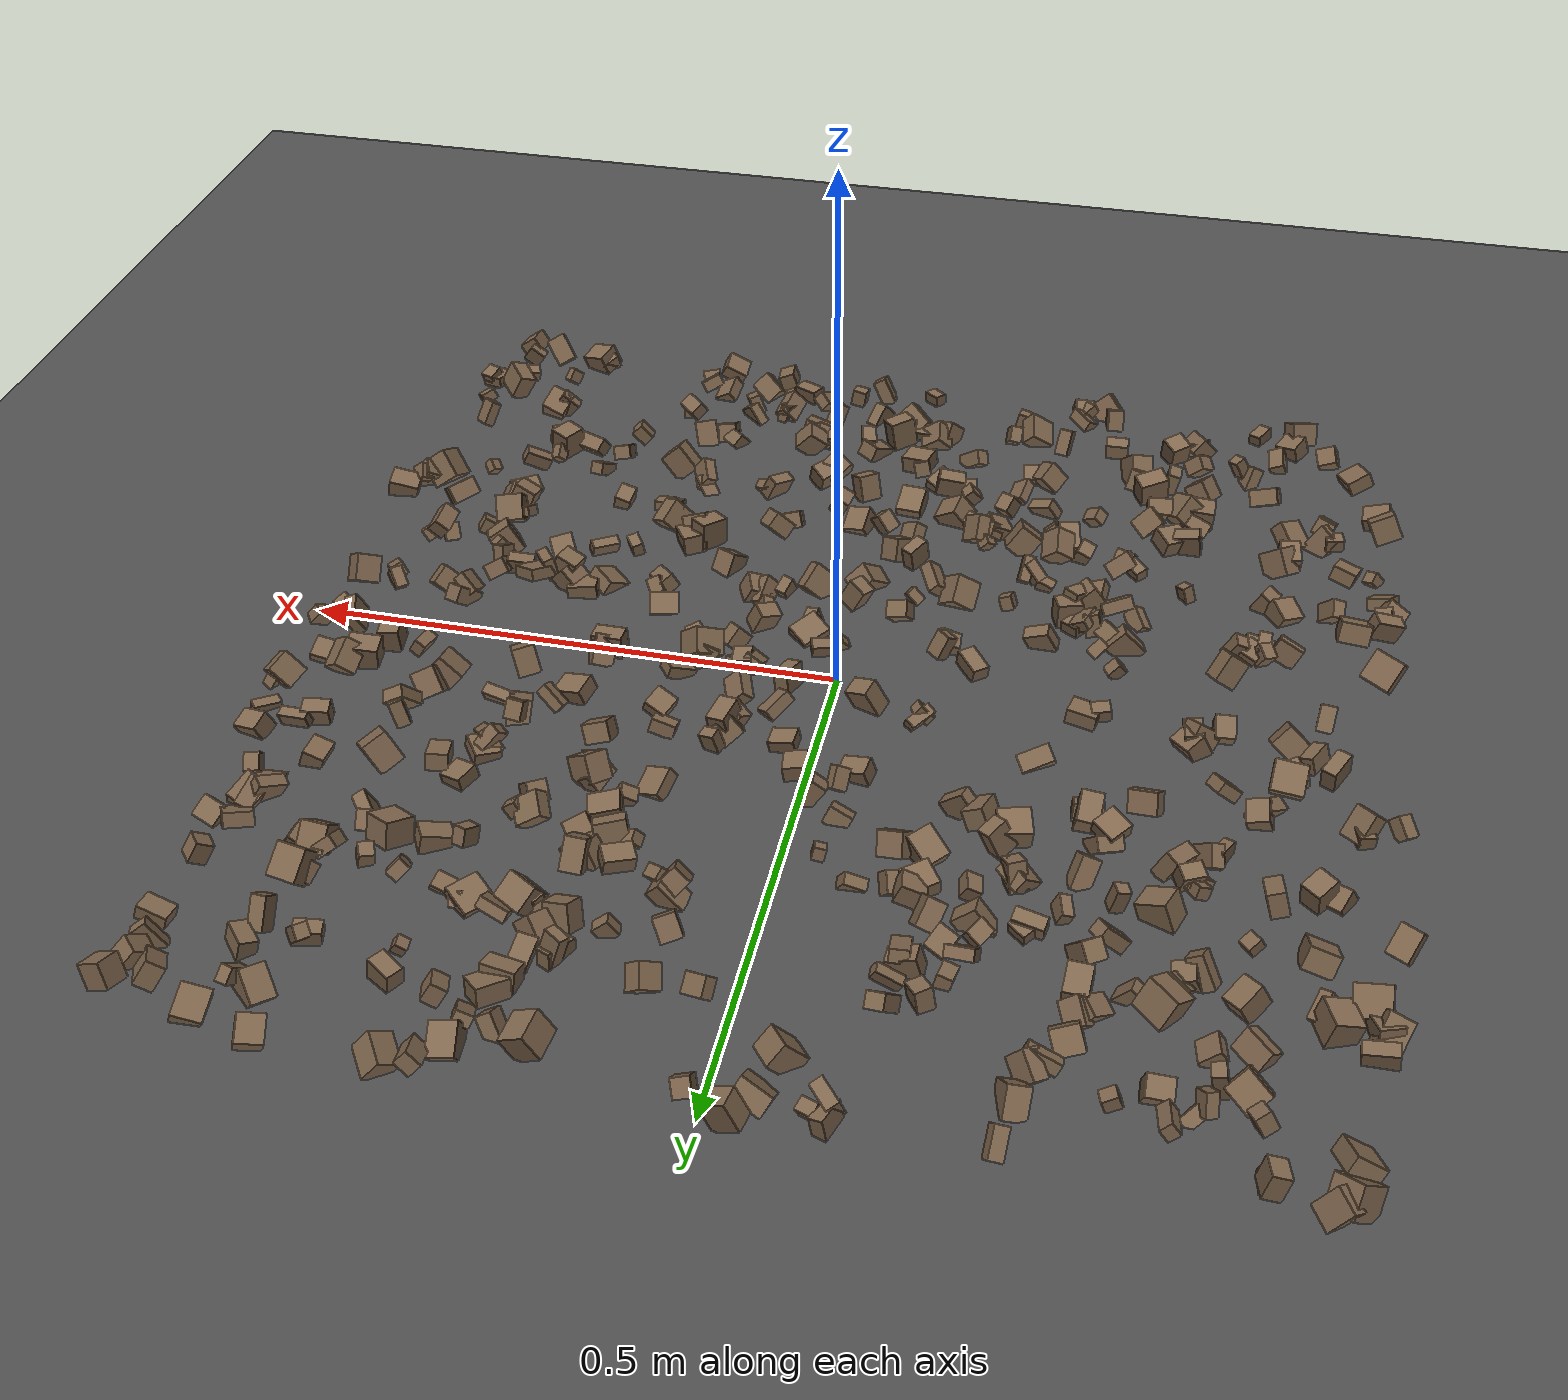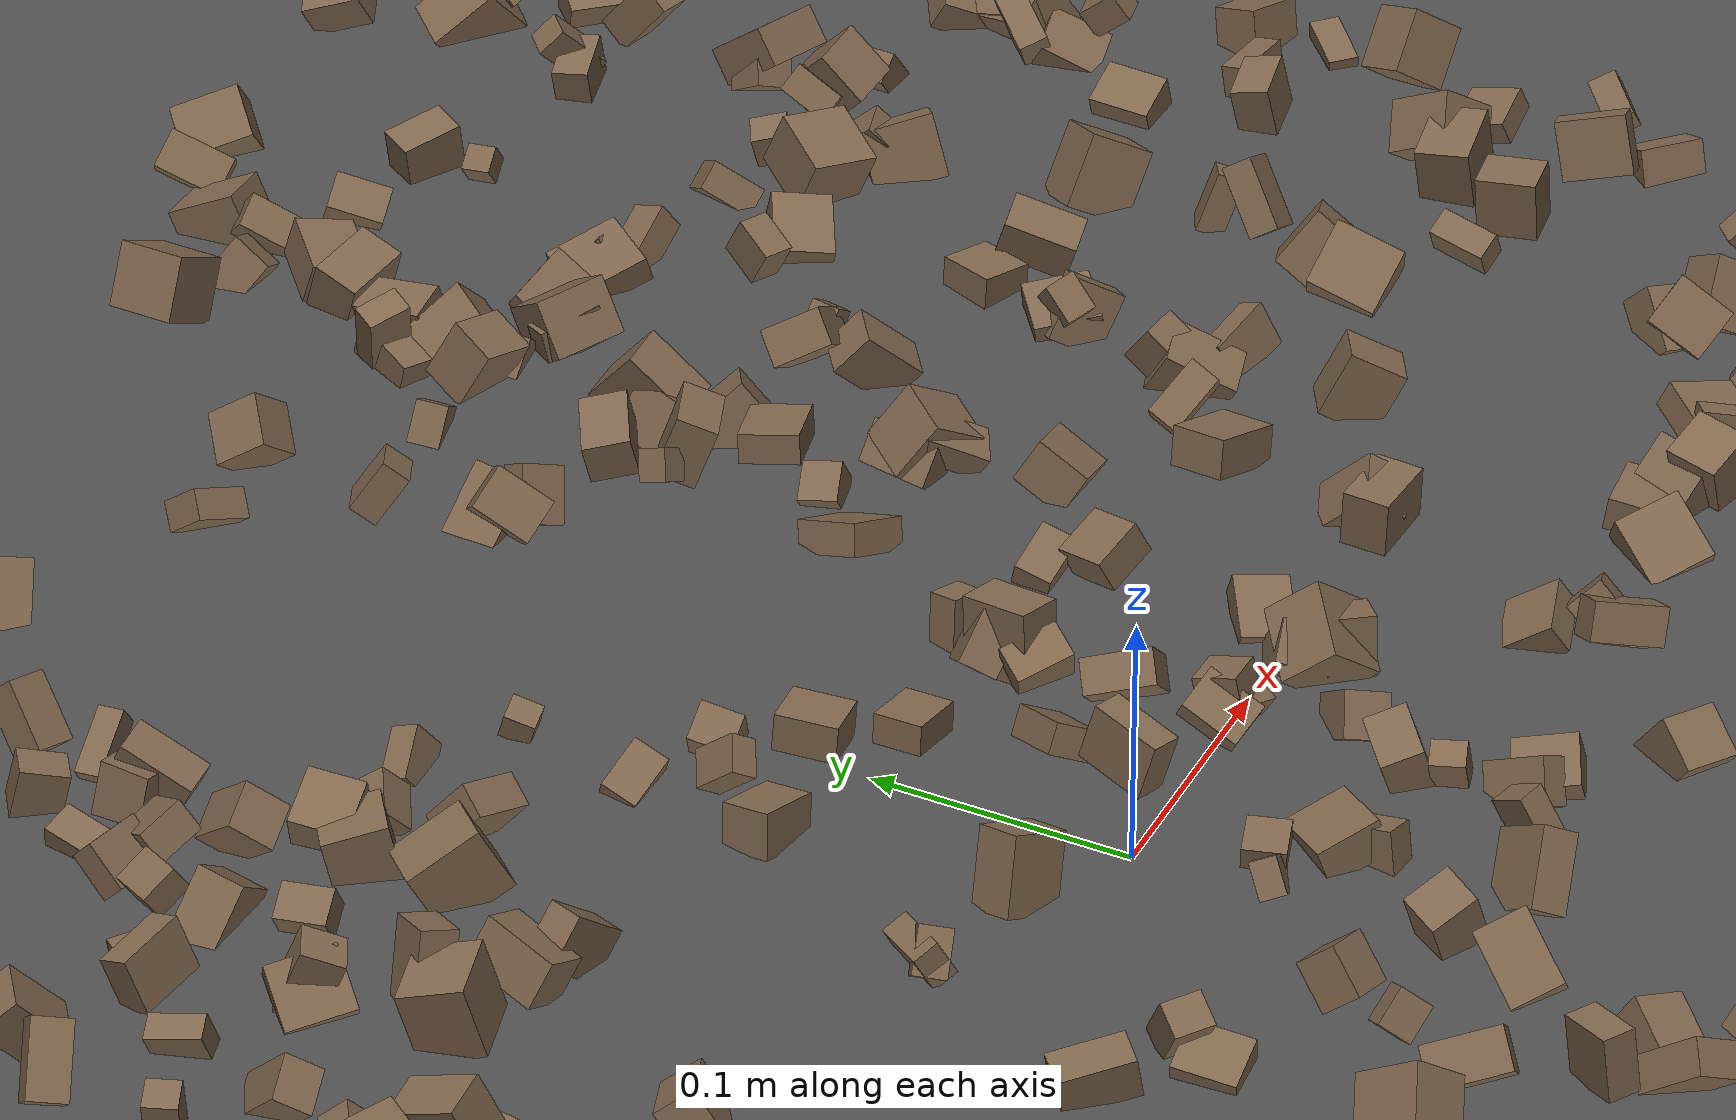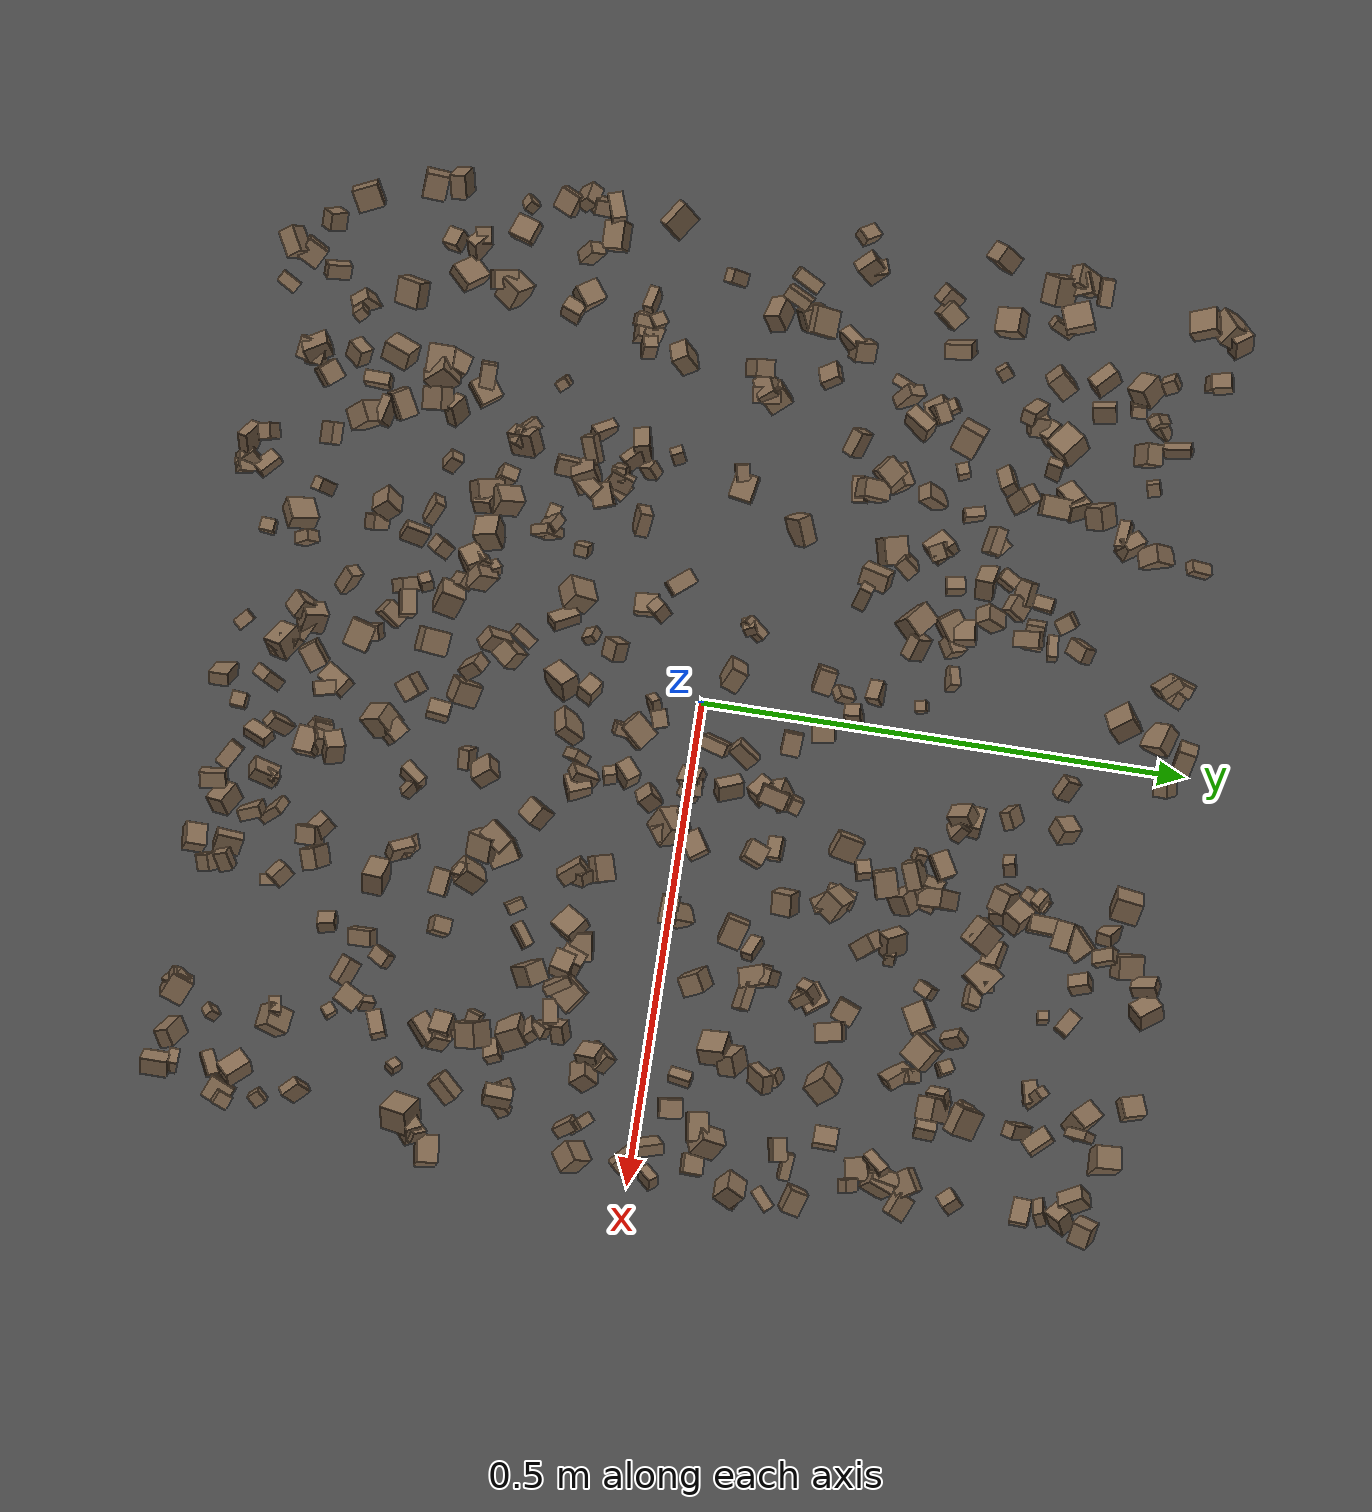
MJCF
<mujoco model="rocky_terrain_scene">
    <compiler angle="radian" inertiafromgeom="true" />
    <option timestep="0.002" gravity="0 0 -9.81" />

    <worldbody>
        <light name="sunlight" pos="5 5 5" dir="-1 -1 -1" diffuse="1 1 1" specular="0.5 0.5 0.5"
            ambient="0.5 0.5 0.5" />

        <geom name="ground_plane" type="plane" size="50 50 0.1" rgba="0.3 0.3 0.3 1" />

        <body name="rocky_terrain_body">

            <geom name="rock1" type="box"
                size="0.013692041512575536 0.00712194500932691 0.005943216000683706"
                pos="-0.34997003794679127 0.4194407637076467 0.0005095328092053064"
                quat="0.48532231053356323 0.20932529862994073 0.21317861958617346 0.09217377125032253"
                rgba="0.5 0.4 0.3 1" />
            <geom name="rock2" type="box"
                size="0.01146009818581378 0.01223926176763756 0.014478405929780093"
                pos="0.19169385704831154 0.3190333329906001 0.006457419010577941"
                quat="0.22702864609115095 0.3982177465137724 0.0197664756448319 0.35498713175024477"
                rgba="0.5 0.4 0.3 1" />
            <geom name="rock3" type="box"
                size="0.00836933405206914 0.014635896066406574 0.010103633762259707"
                pos="0.41502097244610703 -0.4846814408372174 0.01491076991889074"
                quat="0.05854431606868708 0.340910921519358 0.29384994755478333 0.3066948148571716"
                rgba="0.5 0.4 0.3 1" />
            <geom name="rock4" type="box"
                size="0.010942138527485143 0.006714424767598641 0.013624961337328791"
                pos="-0.447409882664382 0.4872066065195383 0.010293663698775919"
                quat="0.15310345134136963 0.2333780094156383 0.5170584534566849 0.09646008578630719"
                rgba="0.5 0.4 0.3 1" />
            <geom name="rock5" type="box"
                size="0.01057158449421689 0.012079592272867836 0.008496335353262606"
                pos="0.4650634114180243 0.44174063885627957 0.00900404848309272"
                quat="0.32658028787914545 0.3312321031182799 0.023045653673178887 0.3191419553293957"
                rgba="0.5 0.4 0.3 1" />
            <geom name="rock6" type="box"
                size="0.006220631513762284 0.007904954207322148 0.010604433433154373"
                pos="0.09254821229424914 -0.22849241101346685 0.006043278125804732"
                quat="0.14234061051206842 0.3539760187623609 0.22043102614245136 0.28325234458311926"
                rgba="0.5 0.4 0.3 1" />
            <geom name="rock7" type="box"
                size="0.008770561452219345 0.008968409247830558 0.007584576882140482"
                pos="-0.11640809344395397 -0.28776585998458726 0.013336032163747567"
                quat="0.36020079054115123 0.2650996486374293 0.2970584096089252 0.0776411512124943"
                rgba="0.5 0.4 0.3 1" />
            <geom name="rock8" type="box"
                size="0.012700827121049717 0.0141038174494778 0.014082229695998903"
                pos="-0.30892319593216133 0.22887524188687924 0.004201634934151047"
                quat="0.2261413319417026 0.3626310929120802 0.24143887011229284 0.16978870503392435"
                rgba="0.5 0.4 0.3 1" />
            <geom name="rock9" type="box"
                size="0.010027313251836508 0.006190461024655919 0.007573438190387679"
                pos="-0.49900594633696993 0.09473417456900424 0.004306205046913175"
                quat="0.2977674204786219 0.03134066559610028 0.33272768460111757 0.33816422932416024"
                rgba="0.5 0.4 0.3 1" />
            <geom name="rock10" type="box"
                size="0.014124252690494759 0.011586430581682405 0.013031204797882216"
                pos="-0.09004874417955366 -0.14238919988923848 0.006785436357603789"
                quat="0.4122396190169396 0.05423206239564812 0.25292782465414637 0.28060049393326586"
                rgba="0.5 0.4 0.3 1" />
            <geom name="rock11" type="box"
                size="0.014816682165226976 0.007971993241204088 0.010060958050149157"
                pos="0.034386064643541325 -0.37377611009021505 0.0031904737059805515"
                quat="0.2999296244606794 0.3506114224717524 0.08826345652470761 0.2611954965428606"
                rgba="0.5 0.4 0.3 1" />
            <geom name="rock12" type="box"
                size="0.010402140387583518 0.010903295089330505 0.00655938213594894"
                pos="-0.32560548033339765 0.31201320777663455 0.005356222037900339"
                quat="0.19164627450071195 0.020547181660252 0.2757421575801862 0.5120643862588498"
                rgba="0.5 0.4 0.3 1" />
            <geom name="rock13" type="box"
                size="0.01437429397718953 0.013652936869038498 0.009584974658984911"
                pos="-0.24143253504493734 0.13795684340921965 0.01226097837694684"
                quat="0.32301578348808063 0.18265973437986155 0.2828853188301405 0.2114391633019173"
                rgba="0.5 0.4 0.3 1" />
            <geom name="rock14" type="box"
                size="0.011973448049537622 0.010120364022398312 0.007892711181809457"
                pos="-0.0901683952525566 -0.07160003474440657 0.0008590272218836841"
                quat="0.04865711485018646 0.41809730540658546 0.4459787720678431 0.08726680767538499"
                rgba="0.5 0.4 0.3 1" />
            <geom name="rock15" type="box"
                size="0.009530150619130998 0.01185559852043197 0.00582223111959081"
                pos="0.027009889363371564 0.09672367665239812 0.007526662515490614"
                quat="0.47145652386085873 0.030525533306261073 0.05326173635146981 0.44475620648141034"
                rgba="0.5 0.4 0.3 1" />
            <geom name="rock16" type="box"
                size="0.00950989281447203 0.008987567947936075 0.008022823829271258"
                pos="0.2666133302600753 -0.2301609754685039 0.007836196647278455"
                quat="0.3373274343456898 0.18758328301342347 0.2486419826857903 0.22644729995509638"
                rgba="0.5 0.4 0.3 1" />
            <geom name="rock17" type="box"
                size="0.014764394954565229 0.008163857220022525 0.006119097129673569"
                pos="-0.06393090929371692 -0.15274396847149796 0.013305396235871824"
                quat="0.17483933182182307 0.23813823350387991 0.4523848717096757 0.1346375629646214"
                rgba="0.5 0.4 0.3 1" />
            <geom name="rock18" type="box"
                size="0.009161323815106547 0.008730833294334078 0.009937644095844323"
                pos="0.10417735033174991 -0.03892158709589433 0.0019387441622782935"
                quat="0.030838700798538773 0.24532407148480911 0.4662071901452602 0.25763003757139197"
                rgba="0.5 0.4 0.3 1" />
            <geom name="rock19" type="box"
                size="0.00662294954512281 0.012283738120144863 0.013578779002816756"
                pos="-0.3867992867386493 0.0956711328034151 0.002178804157553292"
                quat="0.24906937041994145 0.03263475294093811 0.2977998348550309 0.4204960417840896"
                rgba="0.5 0.4 0.3 1" />
            <geom name="rock20" type="box"
                size="0.012177275768956148 0.013745220433730544 0.01472817239743798"
                pos="0.12955643448800114 -0.014823541305853838 0.010315852602116957"
                quat="0.35981528227046355 0.018702354817301862 0.2993684929629117 0.32211386994932295"
                rgba="0.5 0.4 0.3 1" />
            <geom name="rock21" type="box"
                size="0.013333557543660172 0.005506387841118654 0.00945574171275382"
                pos="-0.20588499499551527 -0.11901764902901268 0.00772541882657519"
                quat="0.32323364010568906 0.3409716056868891 0.18324635398553 0.15254840022189187"
                rgba="0.5 0.4 0.3 1" />
            <geom name="rock22" type="box"
                size="0.00755942839932452 0.013958682498021013 0.010212466219596664"
                pos="-0.48537015750618695 -0.16365893216243177 0.013625222249227504"
                quat="0.08202846417874901 0.35760677513538386 0.49909795464928397 0.06126680603658316"
                rgba="0.5 0.4 0.3 1" />
            <geom name="rock23" type="box"
                size="0.006021007434221439 0.007898126159801622 0.014101351800794956"
                pos="0.27602205550354664 0.153776558354057 0.01175817780867024"
                quat="0.15180025675088651 0.13223069198695167 0.5336180044224907 0.18235104683967118"
                rgba="0.5 0.4 0.3 1" />
            <geom name="rock24" type="box"
                size="0.010666991042134498 0.014909381054388111 0.012879223000922927"
                pos="0.09471684569307082 -0.38234816867731136 0.004131527813949388"
                quat="0.37558126815481496 0.07049586629507813 0.2609038487883082 0.29301901676179876"
                rgba="0.5 0.4 0.3 1" />
            <geom name="rock25" type="box"
                size="0.013422904440920744 0.007695171943623302 0.008297053234496877"
                pos="0.15207571166674483 -0.48130516263111556 0.013822120822187148"
                quat="0.17232303144375533 0.2903799812084857 0.29928692018630665 0.2380100671614524"
                rgba="0.5 0.4 0.3 1" />
            <geom name="rock26" type="box"
                size="0.0064678404841049825 0.005925551426015788 0.012657494587645502"
                pos="0.44090317851885963 -0.44096120583817167 0.008222369156527722"
                quat="0.2506442191010534 0.13817148359004938 0.3024471102735885 0.3087371870353086"
                rgba="0.5 0.4 0.3 1" />
            <geom name="rock27" type="box"
                size="0.014353421157899959 0.011304001930973051 0.011714055589731744"
                pos="0.0026097616104171495 -0.4322298492366359 0.007624207240827195"
                quat="0.188143893727005 0.1129693447477987 0.5286840342030851 0.17020272732211122"
                rgba="0.5 0.4 0.3 1" />
            <geom name="rock28" type="box"
                size="0.009595705324146348 0.009865297657550797 0.010238383186892713"
                pos="0.36259640568988005 -0.48658435268269185 0.005933388886830192"
                quat="0.41719518953084855 0.27163151969418853 0.19449490660754729 0.11667838416741567"
                rgba="0.5 0.4 0.3 1" />
            <geom name="rock29" type="box"
                size="0.0050206606188501444 0.011110078592369298 0.007123200602783052"
                pos="0.010992478178534992 -0.04806989525694638 0.0005250547773680186"
                quat="0.314812666243542 0.016588774875530142 0.20580436871238889 0.46279419016853895"
                rgba="0.5 0.4 0.3 1" />
            <geom name="rock30" type="box"
                size="0.011192748120830247 0.009367639992867115 0.014950980669450595"
                pos="0.18315276984290307 -0.17725817635080143 0.006429488027664731"
                quat="0.36857949352762265 0.41779763438772544 0.12077008359496613 0.09285278848968578"
                rgba="0.5 0.4 0.3 1" />
            <geom name="rock31" type="box"
                size="0.008787223352453726 0.008219410785854676 0.0063967110752792345"
                pos="0.25475210884690536 0.27062015732789513 0.014552338923816771"
                quat="0.24549125049465137 0.36263689954368383 0.13638852256571132 0.25548332739595336"
                rgba="0.5 0.4 0.3 1" />
            <geom name="rock32" type="box"
                size="0.014833324233369149 0.010198663037603306 0.006768624824693302"
                pos="-0.03031961413945017 -0.2184806711323436 0.008622274399749897"
                quat="0.43703928195286124 0.009367217925545472 0.25873840510328705 0.29485509501830626"
                rgba="0.5 0.4 0.3 1" />
            <geom name="rock33" type="box"
                size="0.007379475083569091 0.012239515842435964 0.01094417297965899"
                pos="0.3418280082077634 0.4968430141496639 0.010850877463155936"
                quat="0.0007762683613865631 0.3528246698454551 0.13756459873934151 0.508834463053817"
                rgba="0.5 0.4 0.3 1" />
            <geom name="rock34" type="box"
                size="0.012404904502892122 0.008167725744781177 0.014548321782697247"
                pos="-0.2506565181639868 -0.10009661679400217 0.0029069797087117946"
                quat="0.6442827991786357 0.00526347771202137 0.25750550429044505 0.09294821881889771"
                rgba="0.5 0.4 0.3 1" />
            <geom name="rock35" type="box"
                size="0.009640231118767469 0.007624092855923328 0.012763124710520928"
                pos="-0.3964219463826264 -0.2659127172483505 0.00930428049375274"
                quat="0.5234383898129601 0.4073422002878586 0.02869865014579246 0.0405207597533888"
                rgba="0.5 0.4 0.3 1" />
            <geom name="rock36" type="box"
                size="0.0074710873309280414 0.010871736278659623 0.006445225175962195"
                pos="-0.10991680176712659 -0.46557450854447513 0.000177073259517338"
                quat="0.26804167113191907 0.2535668139108758 0.19089342652764044 0.28749808842956476"
                rgba="0.5 0.4 0.3 1" />
            <geom name="rock37" type="box"
                size="0.012893970661128181 0.006853071345021164 0.00613267946040036"
                pos="-0.17910587724760696 -0.23882997183464594 0.00791107704197793"
                quat="0.13773739498929147 0.35894198274484795 0.2072299992863883 0.2960906229794723"
                rgba="0.5 0.4 0.3 1" />
            <geom name="rock38" type="box"
                size="0.0075190482178621905 0.008482423116860252 0.006833501139523999"
                pos="-0.3949662930170207 0.42351944406429076 0.01159505467436546"
                quat="0.09107707784253885 0.27677480405046384 0.34506539972453465 0.2870827183824628"
                rgba="0.5 0.4 0.3 1" />
            <geom name="rock39" type="box"
                size="0.012776411995435635 0.013645806111009611 0.014655371035567938"
                pos="-0.44664909682252685 0.3195215590559495 0.005659507978211531"
                quat="0.405628965621177 0.44029473418046805 0.01998167268544317 0.1340946275129118"
                rgba="0.5 0.4 0.3 1" />
            <geom name="rock40" type="box"
                size="0.005574572657892327 0.007918362374016802 0.009041236638409847"
                pos="0.23422870998992096 -0.1570515757815446 0.004377358469335741"
                quat="0.4178607991017208 0.36037507260731966 0.14110602972312092 0.08065809856783865"
                rgba="0.5 0.4 0.3 1" />
            <geom name="rock41" type="box"
                size="0.009065947265647498 0.013088188216532657 0.010629722059992179"
                pos="0.029606024121289654 -0.2960265917068434 0.010582539729372611"
                quat="0.0987808706691095 0.22317267916150263 0.30090789414856095 0.3771385560208269"
                rgba="0.5 0.4 0.3 1" />
            <geom name="rock42" type="box"
                size="0.010957933094971957 0.009865071200651648 0.013038297840744863"
                pos="-0.32637786259537194 0.018010053608080945 0.007194459096739595"
                quat="0.4977661271108307 0.0025979539891772345 0.2761254724070467 0.22351044649294544"
                rgba="0.5 0.4 0.3 1" />
            <geom name="rock43" type="box"
                size="0.012533517024964958 0.014137378577632323 0.012207088163110771"
                pos="-0.21172624942727047 -0.15279820288811174 0.00978929655360546"
                quat="0.10142950894864283 0.2726686839260645 0.38598558874854955 0.2399162183767431"
                rgba="0.5 0.4 0.3 1" />
            <geom name="rock44" type="box"
                size="0.01381088597850632 0.012234049244993559 0.011364555696722163"
                pos="0.36807969307469346 -0.48619231336826085 0.007963071510101456"
                quat="0.1361846522132761 0.1080620569384353 0.06139107207961107 0.6943622187686775"
                rgba="0.5 0.4 0.3 1" />
            <geom name="rock45" type="box"
                size="0.01497756537419332 0.007604714457208549 0.00863271091908615"
                pos="-0.24406474625663643 0.2007408806921337 0.00423797243527925"
                quat="0.4490972464590336 0.0650000669019581 0.29184530849904866 0.19405737813995957"
                rgba="0.5 0.4 0.3 1" />
            <geom name="rock46" type="box"
                size="0.014594087507335918 0.007318534932334912 0.014589843425399332"
                pos="0.4549744871782073 0.25436085820082144 0.00232888684245799"
                quat="0.17468445462695206 0.42372224948751125 0.3823677790865929 0.019225516798943753"
                rgba="0.5 0.4 0.3 1" />
            <geom name="rock47" type="box"
                size="0.01182579103579027 0.011794619014959106 0.009726867073552158"
                pos="0.4138898749101808 0.030943954796329054 0.01128479553294318"
                quat="0.24121316174038698 0.2261262325832112 0.27918010144642136 0.25348050422998036"
                rgba="0.5 0.4 0.3 1" />
            <geom name="rock48" type="box"
                size="0.006357286891061145 0.012033868309744587 0.005383301820357722"
                pos="0.3675210230093451 0.1319430322329661 0.0081387905004153"
                quat="0.3405504314399489 0.4665548758796508 0.16032681197640197 0.03256788070399836"
                rgba="0.5 0.4 0.3 1" />
            <geom name="rock49" type="box"
                size="0.006200392916059398 0.013743530785608561 0.01281848740244023"
                pos="0.1228463590429042 0.1681542109574512 0.0020266713577903454"
                quat="0.12944092701061582 0.521409570412526 0.010685888119021228 0.33846361445783696"
                rgba="0.5 0.4 0.3 1" />
            <geom name="rock50" type="box"
                size="0.006035962243924216 0.008291317808710934 0.009370057967346466"
                pos="-0.10505853233545237 -0.42528215272088277 0.007903254638813821"
                quat="0.25317330630040374 0.6120195613713112 0.03242714821392621 0.10237998411435896"
                rgba="0.5 0.4 0.3 1" />
            <geom name="rock51" type="box"
                size="0.00840274944643895 0.013199233995329879 0.006832874426213134"
                pos="0.28915558515939077 -0.30650489284661087 0.010727150399944183"
                quat="0.7034355265034238 0.19093749049742362 0.07487304053018552 0.03075394246896714"
                rgba="0.5 0.4 0.3 1" />
            <geom name="rock52" type="box"
                size="0.010729331063954684 0.008685338673249249 0.0115010369315541"
                pos="0.28943880044014214 0.1930429546594883 0.0013032596519541439"
                quat="0.04964376163997794 0.10901870666209902 0.4264970242538533 0.4148405074440698"
                rgba="0.5 0.4 0.3 1" />
            <geom name="rock53" type="box"
                size="0.01436969401556763 0.007756940619257926 0.010873471153291112"
                pos="-0.39711565585716535 0.20516417329406045 0.014162889287514087"
                quat="0.4036000885685063 0.12274457196222763 0.00480888678730006 0.46884645268196606"
                rgba="0.5 0.4 0.3 1" />
            <geom name="rock54" type="box"
                size="0.013964984811287433 0.010025187232022694 0.00638999527315261"
                pos="-0.352005671725923 -0.40175461841341875 0.0006898460523519295"
                quat="0.4769027504455139 0.007508627163493912 0.29738653392692127 0.2182020884640709"
                rgba="0.5 0.4 0.3 1" />
            <geom name="rock55" type="box"
                size="0.011094674251960038 0.008931912085307135 0.012036703123098905"
                pos="-0.4067570008433614 0.05093846313132744 0.004961169168786869"
                quat="0.4830337730757484 0.3228394857837876 0.14829521726796516 0.04583152387249872"
                rgba="0.5 0.4 0.3 1" />
            <geom name="rock56" type="box"
                size="0.014194058861125427 0.00846469207421827 0.011635725424991916"
                pos="0.18507271220436727 0.4169432335904141 0.007665110560264199"
                quat="0.30168800584964084 0.41152642815514817 0.13754123160370163 0.14924433439150933"
                rgba="0.5 0.4 0.3 1" />
            <geom name="rock57" type="box"
                size="0.013584588704347735 0.006401984475505453 0.01024504967385745"
                pos="0.21470328278603157 -0.457512096367373 0.0028506482966676864"
                quat="0.2218007856239999 0.3143784811554211 0.33007887148813253 0.1337418617324465"
                rgba="0.5 0.4 0.3 1" />
            <geom name="rock58" type="box"
                size="0.00714734831105528 0.010744892910698252 0.008194792767900205"
                pos="-0.037466919304724344 0.17434909979378121 0.0005473344787831535"
                quat="0.008133538724971 0.43014217761690254 0.393638171644172 0.16808611201395443"
                rgba="0.5 0.4 0.3 1" />
            <geom name="rock59" type="box"
                size="0.007172275532098038 0.014523223544246792 0.011534352976950334"
                pos="-0.46556658034621257 0.10291505339409823 0.007404853654993284"
                quat="0.28188230302907497 0.4619959592300036 0.0017887472912032467 0.25433299044971824"
                rgba="0.5 0.4 0.3 1" />
            <geom name="rock60" type="box"
                size="0.005912730216961015 0.010698720680229066 0.012781171715454273"
                pos="-0.2570146253004557 -0.29407350024509527 0.008441693074363045"
                quat="0.038392289801200005 0.4533034091955564 0.2734900910488374 0.23481420995440616"
                rgba="0.5 0.4 0.3 1" />
            <geom name="rock61" type="box"
                size="0.011481525738955486 0.013849707577549657 0.010764774609759813"
                pos="-0.17371304920811625 -0.22913403715408154 0.013405572564253506"
                quat="0.04056721365642985 0.2525243684578204 0.14695356547022487 0.559954852415525"
                rgba="0.5 0.4 0.3 1" />
            <geom name="rock62" type="box"
                size="0.010441534824447644 0.013303146846069782 0.011604893623569423"
                pos="0.282689153394023 0.03681485398494766 0.007597469107491586"
                quat="0.3146345000541739 0.49399063753165073 0.1473973865704079 0.04397747584376744"
                rgba="0.5 0.4 0.3 1" />
            <geom name="rock63" type="box"
                size="0.00832166463968663 0.01265028327548431 0.011066486340253735"
                pos="-0.20030073212021116 -0.14638676252126315 0.012724966871283928"
                quat="0.1452895336875851 0.1122974144345893 0.32796442258194325 0.41444862929588233"
                rgba="0.5 0.4 0.3 1" />
            <geom name="rock64" type="box"
                size="0.009880075684372484 0.011317897134076941 0.006840571726212072"
                pos="-0.07294675671486095 -0.3171009341629648 0.003084429385057157"
                quat="0.07283541711274812 0.3596310850589523 0.1621458454832033 0.4053876523450963"
                rgba="0.5 0.4 0.3 1" />
            <geom name="rock65" type="box"
                size="0.005352007667070846 0.006482320143319187 0.013797985550945274"
                pos="0.45465031104379305 0.15668587587498206 0.008744235370368829"
                quat="0.274464582727234 0.24570870126827046 0.2755274035681244 0.2042993124363711"
                rgba="0.5 0.4 0.3 1" />
            <geom name="rock66" type="box"
                size="0.007257129768512628 0.010290596793270079 0.010848881760718201"
                pos="-0.37620038251174004 -0.19190017443835328 0.004798773066321772"
                quat="0.16562658380920328 0.13951686264924174 0.6928212085053345 0.0020353450362204754"
                rgba="0.5 0.4 0.3 1" />
            <geom name="rock67" type="box"
                size="0.007309354957175394 0.013495478359081218 0.006253133000556066"
                pos="-0.3506844078898127 -0.10948353065909922 0.008051238404848894"
                quat="0.2943284445566863 0.14816350546366583 0.2345833813085867 0.3229246686710612"
                rgba="0.5 0.4 0.3 1" />
            <geom name="rock68" type="box"
                size="0.009668284666324457 0.012539995857681436 0.012111603960966798"
                pos="0.15152670399448653 0.33525881647244626 0.009752564265585408"
                quat="0.20077473386984288 0.37132195124365935 0.18862448808913543 0.23927882679736223"
                rgba="0.5 0.4 0.3 1" />
            <geom name="rock69" type="box"
                size="0.008356992100044522 0.005332046070358175 0.00559422693561528"
                pos="0.24615977857176408 -0.4102360185099423 0.0027046939635756396"
                quat="0.19931170687093772 0.2536673174935115 0.25311603403260197 0.2939049416029489"
                rgba="0.5 0.4 0.3 1" />
            <geom name="rock70" type="box"
                size="0.012084330583124612 0.005002210444535723 0.009625280385433626"
                pos="-0.21061903648649227 -0.11672592756401112 0.013832193359566671"
                quat="0.20865475983179665 0.37570364691315006 0.2781286185257113 0.13751297472934196"
                rgba="0.5 0.4 0.3 1" />
            <geom name="rock71" type="box"
                size="0.008449468620187073 0.005850989085310243 0.013913354141609463"
                pos="0.04487903801215898 0.050345442398955664 0.005858440233926852"
                quat="0.019561952982341427 0.2483902408274169 0.3996524511609487 0.3323953550292929"
                rgba="0.5 0.4 0.3 1" />
            <geom name="rock72" type="box"
                size="0.006649506035395738 0.006157036511018113 0.010856498427499254"
                pos="0.4381806454651015 -0.14124630335264132 0.004539502291497529"
                quat="0.05629969696084729 0.28912357791085713 0.3549065645066832 0.29967016062161245"
                rgba="0.5 0.4 0.3 1" />
            <geom name="rock73" type="box"
                size="0.010626125747571203 0.006180735698682467 0.01380629765117097"
                pos="-0.20930473918310744 0.26982960133617273 0.010244816939826996"
                quat="0.12222052950263601 0.4068684830246197 0.03617507411721494 0.4347359133555293"
                rgba="0.5 0.4 0.3 1" />
            <geom name="rock74" type="box"
                size="0.01174358993173868 0.012951575724213547 0.011810572087854979"
                pos="0.4784552754306709 -0.06058213086975528 0.009479943119386481"
                quat="0.0854753210425515 0.22487789615936538 0.21774634227889883 0.47190044051918434"
                rgba="0.5 0.4 0.3 1" />
            <geom name="rock75" type="box"
                size="0.006265070557730275 0.006731286079564289 0.011262230981135317"
                pos="0.44942164529259987 -0.07160233878217459 0.005122063656657462"
                quat="0.30379031260343914 0.4344411401106328 0.21841347736901023 0.043355069916917816"
                rgba="0.5 0.4 0.3 1" />
            <geom name="rock76" type="box"
                size="0.005715202093822579 0.010408385284643325 0.010691276352837158"
                pos="-0.3509073484290929 0.07829068081951107 0.006383067030512005"
                quat="0.5388216331169469 0.009940403711522982 0.26366112176139916 0.1875768414101309"
                rgba="0.5 0.4 0.3 1" />
            <geom name="rock77" type="box"
                size="0.012020943824425402 0.01222504910545077 0.011781127828465514"
                pos="-0.39294981945947915 -0.17863080029063538 0.0015271030477554785"
                quat="0.24765632045875519 0.0918797659333829 0.33263433320020963 0.3278295804076523"
                rgba="0.5 0.4 0.3 1" />
            <geom name="rock78" type="box"
                size="0.013497908017643296 0.010232389850005871 0.006897511670950391"
                pos="0.08160385274842608 0.04028417207449331 0.009366655026160483"
                quat="0.31474036300209085 0.06690091887504356 0.21701578901579846 0.4013429291070672"
                rgba="0.5 0.4 0.3 1" />
            <geom name="rock79" type="box"
                size="0.011697210654818869 0.013160477837797578 0.014126445544061776"
                pos="0.1569333795516341 0.2573288682807576 0.001904534327023322"
                quat="0.33569752499248356 0.10448383304748343 0.5597940951327179 2.4546827314957828e-05"
                rgba="0.5 0.4 0.3 1" />
            <geom name="rock80" type="box"
                size="0.01439836704458811 0.013970378489901972 0.009917239485218231"
                pos="0.16726034812635837 -0.18533803003700877 0.012202586227973771"
                quat="0.31720525599589944 0.35633264908987405 0.1474458320260389 0.1790162628881877"
                rgba="0.5 0.4 0.3 1" />
            <geom name="rock81" type="box"
                size="0.006293515833567758 0.011058237836746495 0.006025641568780606"
                pos="-0.27479473506429264 0.22728565311759574 0.00956313645508786"
                quat="0.22990706771122063 0.1791099072405882 0.2574338201945276 0.33354920485366346"
                rgba="0.5 0.4 0.3 1" />
            <geom name="rock82" type="box"
                size="0.010664735639732362 0.0068625478338167865 0.013756956479565041"
                pos="0.04506865754132727 -0.48814901636473684 0.005764655504690917"
                quat="0.3745939950195604 0.1703080361563725 0.03730717669913984 0.41779079212492726"
                rgba="0.5 0.4 0.3 1" />
            <geom name="rock83" type="box"
                size="0.014184234106265757 0.007883271213512774 0.010281498562423516"
                pos="0.39069884179164516 0.40835015644722716 0.00223294360132964"
                quat="0.035950398751760204 0.2632152479591386 0.5970546412720443 0.10377971201705688"
                rgba="0.5 0.4 0.3 1" />
            <geom name="rock84" type="box"
                size="0.007389428682800611 0.01443203788049503 0.00746008591078422"
                pos="0.19041113570123724 -0.10479608939525287 0.007697330163992224"
                quat="0.5853482324819597 0.031167497567911935 0.15814905540873112 0.22533521454139732"
                rgba="0.5 0.4 0.3 1" />
            <geom name="rock85" type="box"
                size="0.00859455558179104 0.01447844646425062 0.0076711539447696445"
                pos="0.13498776142885704 -0.022818704210344154 0.006592725569498148"
                quat="0.14604583538276947 0.1878820786784142 0.36895960701156283 0.2971124789272535"
                rgba="0.5 0.4 0.3 1" />
            <geom name="rock86" type="box"
                size="0.011971470070494903 0.007416699353106164 0.01291205014375833"
                pos="0.21230601886654132 0.22994503657031395 0.013138914977734445"
                quat="0.22145736782896203 0.2073594112714642 0.4343958508359034 0.13678737006367042"
                rgba="0.5 0.4 0.3 1" />
            <geom name="rock87" type="box"
                size="0.00656474271238648 0.012487385814436305 0.014056796198454687"
                pos="-0.47830437536326564 0.34262825902775973 0.00262875149678856"
                quat="0.2500013606755234 0.24970844471664044 0.28119957246518235 0.2190906221426538"
                rgba="0.5 0.4 0.3 1" />
            <geom name="rock88" type="box"
                size="0.013655513202886261 0.00534573977027125 0.0051764832350174265"
                pos="0.37117375890605897 -0.18782391356085948 0.00707359944255546"
                quat="0.15780225655697225 0.33498655642816244 0.289183501626718 0.2180276853881473"
                rgba="0.5 0.4 0.3 1" />
            <geom name="rock89" type="box"
                size="0.014604549478593742 0.00716154753816724 0.007227142879178335"
                pos="0.38260522364879546 0.38436237199532464 0.012539954270190492"
                quat="0.35969514390938556 0.16559509028783725 0.38420364932558354 0.09050611647719367"
                rgba="0.5 0.4 0.3 1" />
            <geom name="rock90" type="box"
                size="0.005915611847570474 0.005916572907139563 0.005325054627873225"
                pos="-0.03046836143587195 0.22178425891954312 0.005685201695720898"
                quat="0.21822626629420297 0.24038544898761735 0.20378376199958614 0.3376045227185935"
                rgba="0.5 0.4 0.3 1" />
            <geom name="rock91" type="box"
                size="0.01006252974419243 0.012695993427694237 0.010440712418204198"
                pos="-0.27464408306780774 -0.42778392995271886 0.010156882936795427"
                quat="0.1910340206667034 0.1327797518546241 0.3763957678770844 0.299790459601588"
                rgba="0.5 0.4 0.3 1" />
            <geom name="rock92" type="box"
                size="0.010188886689131444 0.013688098369103403 0.0065934587997113605"
                pos="-0.34212495872397775 0.161125514820617 0.004377874704007154"
                quat="0.36758757460128433 0.05280532356897899 0.3045435893209952 0.2750635125087414"
                rgba="0.5 0.4 0.3 1" />
            <geom name="rock93" type="box"
                size="0.007534661980867363 0.008828425304541655 0.009609358612541665"
                pos="0.1833113228131671 -0.36523434781978115 0.0020672268086925874"
                quat="0.4092199971252118 0.27409494504941245 0.27730197303184695 0.039383084793528755"
                rgba="0.5 0.4 0.3 1" />
            <geom name="rock94" type="box"
                size="0.009400876265333667 0.01374797996450879 0.012186639297878409"
                pos="-0.01950717854708406 0.4958913501210015 0.014492148484868595"
                quat="0.2131879140640481 0.3351964441908067 0.28015319691211504 0.1714624448330302"
                rgba="0.5 0.4 0.3 1" />
            <geom name="rock95" type="box"
                size="0.01014875505595246 0.006434478597188031 0.013578454398584978"
                pos="-0.2869590532068256 0.11601427024867283 0.013175979550554115"
                quat="0.3494774627152786 0.18893017561563705 0.42453033528003525 0.03706202638904914"
                rgba="0.5 0.4 0.3 1" />
            <geom name="rock96" type="box"
                size="0.00999192299046385 0.011334572457433821 0.01271571078204195"
                pos="-0.37934821863651924 0.3127364916847951 0.009598001708301853"
                quat="0.07444963458015083 0.20527602468238454 0.42417900196312913 0.2960953387743356"
                rgba="0.5 0.4 0.3 1" />
            <geom name="rock97" type="box"
                size="0.01414058118594395 0.009175085588107833 0.01214922593741044"
                pos="-0.16635584466136388 0.26869479762034465 0.0006855792532025285"
                quat="0.29301429809827645 0.039582424903437274 0.62112886875565 0.046274408242636345"
                rgba="0.5 0.4 0.3 1" />
            <geom name="rock98" type="box"
                size="0.006068702005675827 0.012713407518646871 0.010536934802709348"
                pos="0.3788518994807506 -0.3837873943015646 0.00883599706742969"
                quat="0.3323459427066638 0.13288546912197083 0.17012650932650028 0.36464207884486516"
                rgba="0.5 0.4 0.3 1" />
            <geom name="rock99" type="box"
                size="0.006678666539424839 0.014840461573358225 0.007912319150269595"
                pos="0.1939972783653019 -0.09948877858508831 0.003035372448332412"
                quat="0.5890761261601892 0.22673405501750013 0.15774481284798902 0.026445005974321575"
                rgba="0.5 0.4 0.3 1" />
            <geom name="rock100" type="box"
                size="0.009159347704192359 0.011666359466434193 0.007705092547843314"
                pos="-0.1375541572559027 0.3559632130364684 0.0040763063493362795"
                quat="0.12371102605916144 0.21788529983796112 0.31753142087332276 0.3408722532295547"
                rgba="0.5 0.4 0.3 1" />
            <geom name="rock101" type="box"
                size="0.012395999039371889 0.0070928795623082744 0.011530752557910424"
                pos="-0.45031532932343965 -0.25250833430294983 0.005340274418078669"
                quat="0.2861920161182484 0.29422442509290314 0.14967456605281684 0.26990899273603164"
                rgba="0.5 0.4 0.3 1" />
            <geom name="rock102" type="box"
                size="0.014045821233322639 0.012585332353752147 0.012555801239881339"
                pos="0.1385304554569493 0.46027748927842904 0.014016846162583653"
                quat="0.4270891301563018 0.09198343758436002 0.11787810232153045 0.36304932993780786"
                rgba="0.5 0.4 0.3 1" />
            <geom name="rock103" type="box"
                size="0.008144199308198187 0.0076285653630502916 0.007241395254117964"
                pos="0.06956105711633398 -0.46781925313328643 0.008646051073204689"
                quat="0.503248538264532 0.05228935063623024 0.4338800583564424 0.01058205274279545"
                rgba="0.5 0.4 0.3 1" />
            <geom name="rock104" type="box"
                size="0.006186215302220108 0.013362399091236578 0.01107635145424995"
                pos="-0.27521627956413053 -0.37758651105026353 0.006155765016055475"
                quat="0.09199897733937185 0.020219731075054787 0.8235212592836113 0.06426003230196202"
                rgba="0.5 0.4 0.3 1" />
            <geom name="rock105" type="box"
                size="0.009501774449620215 0.013483673425412783 0.013222605935021507"
                pos="-0.12136188039739737 0.3254978199721261 0.0016176781455100669"
                quat="0.20385644080168816 0.29949511254067757 0.2770278545572987 0.21962059210033555"
                rgba="0.5 0.4 0.3 1" />
            <geom name="rock106" type="box"
                size="0.0066962634723826304 0.007255388808871005 0.011242552779689281"
                pos="0.13558654320364205 0.09659655669421452 0.0042700261092213304"
                quat="0.5019188049400969 0.06114617921577129 0.38224372941138957 0.05469128643274232"
                rgba="0.5 0.4 0.3 1" />
            <geom name="rock107" type="box"
                size="0.010863260772194837 0.011752764388093723 0.010505606960676164"
                pos="-0.15157553966642978 -0.3492499044793954 0.01132844156258423"
                quat="0.30168856465067806 0.39505262764785837 0.296321228506817 0.006937579194646572"
                rgba="0.5 0.4 0.3 1" />
            <geom name="rock108" type="box"
                size="0.009740578517805982 0.00930167592465809 0.012687278441690465"
                pos="0.4880490293488281 0.16982225257505446 0.004872821588955463"
                quat="0.28435319497756556 0.28155307416985786 0.2839677549988895 0.15012597585368703"
                rgba="0.5 0.4 0.3 1" />
            <geom name="rock109" type="box"
                size="0.009542230798023674 0.005230920093283971 0.012368310518268545"
                pos="-0.1618856262941779 0.3090204989913795 0.008310294696932785"
                quat="0.1656807346912672 0.3778799214691448 0.13728391137984206 0.319155432459746"
                rgba="0.5 0.4 0.3 1" />
            <geom name="rock110" type="box"
                size="0.007946663824412888 0.007340407669144488 0.006758812731727555"
                pos="0.4791879859866186 -0.22247770116341392 0.01340636123134379"
                quat="0.34952063269577377 9.940031212791452e-05 0.28154381469750245 0.3688361522945959"
                rgba="0.5 0.4 0.3 1" />
            <geom name="rock111" type="box"
                size="0.007382641346448627 0.0074790601120201935 0.01060518514078125"
                pos="0.35444092591499066 -0.09220283542851138 0.0058342739833268376"
                quat="0.09479815509979429 0.36496980886840286 0.28104282754789495 0.25918920848390786"
                rgba="0.5 0.4 0.3 1" />
            <geom name="rock112" type="box"
                size="0.011578311539132328 0.008849357320562877 0.005902470459585744"
                pos="0.029135473920967492 0.38156517640904175 0.0063747788190022135"
                quat="0.08468323918165653 0.15882585124105442 0.19363721138484744 0.5628536981924416"
                rgba="0.5 0.4 0.3 1" />
            <geom name="rock113" type="box"
                size="0.010114786139078402 0.012616803955096574 0.011159277422315123"
                pos="0.36702883231771677 -0.21163800714273318 0.0075768269042261385"
                quat="0.29173500913201805 0.24259571505292618 0.15511502362535512 0.31055425218970056"
                rgba="0.5 0.4 0.3 1" />
            <geom name="rock114" type="box"
                size="0.012965318670502709 0.014747435050493942 0.012288290737455913"
                pos="0.3654336319073258 0.18157803961415586 0.007440815752104083"
                quat="0.0362255463362194 0.2650280329355432 0.371799714003608 0.3269467067246294"
                rgba="0.5 0.4 0.3 1" />
            <geom name="rock115" type="box"
                size="0.009984399179490996 0.011293316409425954 0.01203654039347858"
                pos="-0.30172196458407696 -0.3010096832268294 0.0004666956981404996"
                quat="0.16121416002347658 0.46081128270449273 0.34200071864747394 0.03597383862455669"
                rgba="0.5 0.4 0.3 1" />
            <geom name="rock116" type="box"
                size="0.01204434643067779 0.009019578707347146 0.009443082062918596"
                pos="0.07404263312496318 0.281098703200082 0.011005950583919446"
                quat="0.024227389823605353 0.37141112589472003 0.35488605647170424 0.24947542780997037"
                rgba="0.5 0.4 0.3 1" />
            <geom name="rock117" type="box"
                size="0.007543704994393734 0.01304563494852191 0.011033371392047353"
                pos="0.08091016766465942 0.09446199042988734 0.00734725443111723"
                quat="0.276280929909348 0.20382985049210295 0.07094861910377427 0.44894060049477486"
                rgba="0.5 0.4 0.3 1" />
            <geom name="rock118" type="box"
                size="0.009576372394456458 0.005412882637639857 0.007502908909616794"
                pos="-0.17183903916095855 0.28970531997702087 0.011418638384206294"
                quat="0.4099840475841051 0.21654584451496764 0.15864175837127742 0.2148283495296499"
                rgba="0.5 0.4 0.3 1" />
            <geom name="rock119" type="box"
                size="0.009388700060432562 0.014533929596698046 0.013148667747822005"
                pos="0.44168401374195443 -0.4147186853769619 0.014278149108898588"
                quat="0.018373260144319167 0.5875319548385104 0.23555342981684474 0.15854135520032564"
                rgba="0.5 0.4 0.3 1" />
            <geom name="rock120" type="box"
                size="0.007432832488732673 0.01169445065533298 0.012673967741440306"
                pos="0.3359646016640965 -0.10505328472634545 0.0007381179576119917"
                quat="0.24876105323248626 0.2136571100890503 0.25389620129384677 0.2836856353846167"
                rgba="0.5 0.4 0.3 1" />
            <geom name="rock121" type="box"
                size="0.009543166330176059 0.009637733184944621 0.007464892989186735"
                pos="-0.40198594015077904 0.46894073650352786 0.0022094560640705902"
                quat="0.2944848250054539 0.18569450646002666 0.27481359622702906 0.24500707230749033"
                rgba="0.5 0.4 0.3 1" />
            <geom name="rock122" type="box"
                size="0.010756815077456006 0.0052452875044026286 0.014118801534978798"
                pos="-0.2453474679826959 -0.3649392010923479 0.007756777005884816"
                quat="0.44870164511785254 0.1299777371611716 0.3717175522417495 0.049603065479226306"
                rgba="0.5 0.4 0.3 1" />
            <geom name="rock123" type="box"
                size="0.005258494347413996 0.005814150625949219 0.009928110680208106"
                pos="0.131012706528282 -0.28115641914103306 0.006467741936405278"
                quat="0.29827892783075954 0.3243225036942698 0.32485655284405507 0.0525420156309156"
                rgba="0.5 0.4 0.3 1" />
            <geom name="rock124" type="box"
                size="0.011548643661697295 0.009011561678409604 0.014279008497352346"
                pos="0.2646931116130151 -0.08360549738258927 0.0005331673367929751"
                quat="0.2075224620005352 0.26189489585266457 0.2660135815905899 0.26456906055621043"
                rgba="0.5 0.4 0.3 1" />
            <geom name="rock125" type="box"
                size="0.010870633780483304 0.01114556998323201 0.0088300978067289"
                pos="-0.11151251099837267 0.2541899393390137 0.010873576392317463"
                quat="0.05821432842712679 0.3847977746974237 0.44026410353452966 0.11672379334091985"
                rgba="0.5 0.4 0.3 1" />
            <geom name="rock126" type="box"
                size="0.011059587588278432 0.009129581759142538 0.01174456465675145"
                pos="0.1884228089412716 0.11491839510234303 0.005248631070451709"
                quat="0.14505984119027424 0.3479708195250065 0.2326196407551306 0.27434969852958874"
                rgba="0.5 0.4 0.3 1" />
            <geom name="rock127" type="box"
                size="0.011479480780748355 0.009254469095562259 0.00943955686438319"
                pos="0.1942285554402322 -0.3758904854093461 0.004003517310791657"
                quat="0.15771146662948554 0.32798717056774446 0.21460942988657217 0.2996919329161979"
                rgba="0.5 0.4 0.3 1" />
            <geom name="rock128" type="box"
                size="0.01331007207486145 0.014846194369869212 0.012745802560711903"
                pos="-0.45936319041875795 0.47443039221961514 0.00912521119737702"
                quat="0.3381080825289235 0.2834997494207437 0.3698000296553222 0.008592138395010683"
                rgba="0.5 0.4 0.3 1" />
            <geom name="rock129" type="box"
                size="0.008405153411428886 0.006919582450437049 0.012128149298368144"
                pos="0.17043402346734515 0.44760038697004056 0.0014247383321115059"
                quat="0.38972801443865596 0.2159402552375065 0.0006886606966626848 0.39364306962717494"
                rgba="0.5 0.4 0.3 1" />
            <geom name="rock130" type="box"
                size="0.01027631650325615 0.011810034078073836 0.011984791800685632"
                pos="-0.19396521251418763 -0.1330419855456273 0.00941577520865671"
                quat="0.19489592351325286 0.21899594067722106 0.27296976024037073 0.31313837556915536"
                rgba="0.5 0.4 0.3 1" />
            <geom name="rock131" type="box"
                size="0.0063262525131018476 0.013006923816436644 0.005945241457029471"
                pos="0.34602606962023685 0.39825599546155543 0.012168420963222695"
                quat="0.3002471596357553 0.00913392925792189 0.3867644463900581 0.3038544647162647"
                rgba="0.5 0.4 0.3 1" />
            <geom name="rock132" type="box"
                size="0.01275948307184418 0.006018665254366755 0.00740351251792057"
                pos="-0.17384877129411902 -0.47670679857621634 0.0035739762972908057"
                quat="0.20776967150428993 0.06250337552343388 0.2802791600826241 0.44944779288965203"
                rgba="0.5 0.4 0.3 1" />
            <geom name="rock133" type="box"
                size="0.011635409800746087 0.005217944728200732 0.0070333861057501465"
                pos="-0.17425573280524376 -0.497131650841505 0.004708114765344644"
                quat="0.07604855356041242 0.22009437612568183 0.4167852490654262 0.2870718212484797"
                rgba="0.5 0.4 0.3 1" />
            <geom name="rock134" type="box"
                size="0.0063047653207443585 0.01211485970679125 0.011522884846578249"
                pos="-0.03899873099295115 -0.19073878022836122 0.011653679084593934"
                quat="0.10746429959245442 0.12240255394208051 0.4241643494508468 0.3459687970146182"
                rgba="0.5 0.4 0.3 1" />
            <geom name="rock135" type="box"
                size="0.0148666465294971 0.011384062464037486 0.009867705713194001"
                pos="-0.18187622073560672 -0.25031728064837055 0.006537844281033518"
                quat="0.28789333781626936 0.15556327241455045 0.31793552027047167 0.2386078694987085"
                rgba="0.5 0.4 0.3 1" />
            <geom name="rock136" type="box"
                size="0.014418883478972595 0.009105836611200867 0.010471566784299679"
                pos="-0.2529819176237069 0.3253663392839433 0.010977210232723102"
                quat="0.2769022432616075 0.2360337945683667 0.26499125143232943 0.22207271073769638"
                rgba="0.5 0.4 0.3 1" />
            <geom name="rock137" type="box"
                size="0.0068500760733120735 0.01333767716366389 0.008393417386094573"
                pos="-0.11144608401597056 0.37366407666119517 0.012541532112869538"
                quat="0.3212616720619228 0.2178876547171718 0.36895518873022504 0.09189548449068036"
                rgba="0.5 0.4 0.3 1" />
            <geom name="rock138" type="box"
                size="0.00861225583574267 0.009479627985371938 0.009549149686631545"
                pos="-0.430761919097542 -0.4465402669676676 0.009019533160179756"
                quat="0.09644143659293587 0.45537594504095813 0.14054217163942587 0.30764044672668006"
                rgba="0.5 0.4 0.3 1" />
            <geom name="rock139" type="box"
                size="0.008133260008733729 0.006151703389138485 0.00692878973083292"
                pos="0.4640147576502305 0.22236791377482168 0.011843388271515248"
                quat="0.3144867524783929 0.13418198440988022 0.3637212149232791 0.18761004818844776"
                rgba="0.5 0.4 0.3 1" />
            <geom name="rock140" type="box"
                size="0.007986000830513474 0.005568711609209789 0.013377893741829586"
                pos="0.18095893265711172 0.15580011828882678 0.008843792188942674"
                quat="0.2771384383800406 0.5021377832293155 0.09024591014790476 0.13047786824273924"
                rgba="0.5 0.4 0.3 1" />
            <geom name="rock141" type="box"
                size="0.007570901910868105 0.00640425008178169 0.014383906012772642"
                pos="-0.27231664597036764 0.2734483331577433 0.013299710760218584"
                quat="0.2218456386468552 0.1475687688022994 0.15613102119377995 0.4744545713570655"
                rgba="0.5 0.4 0.3 1" />
            <geom name="rock142" type="box"
                size="0.012534806452695942 0.008295945631154293 0.012919360545401028"
                pos="-0.4868418495182376 -0.32360734386746404 0.014428066564872742"
                quat="0.3286364153978648 0.04205780741746841 0.5279244649530314 0.10138131223163538"
                rgba="0.5 0.4 0.3 1" />
            <geom name="rock143" type="box"
                size="0.008603966220229808 0.01369997468482751 0.007813779894039965"
                pos="-0.48671069995863814 -0.18034300663350133 0.005864879947982728"
                quat="0.2575829883102527 0.25694565144277604 0.3116548320850405 0.17381652816193072"
                rgba="0.5 0.4 0.3 1" />
            <geom name="rock144" type="box"
                size="0.007307407915007903 0.010422286539976566 0.010835646801223127"
                pos="-0.4930394531922747 -0.19333441297437692 0.007192834277735276"
                quat="0.42618925628966786 0.15693341115635337 0.21379123086260582 0.20308610169137287"
                rgba="0.5 0.4 0.3 1" />
            <geom name="rock145" type="box"
                size="0.014940315435620622 0.01268980628861157 0.010295581781329598"
                pos="-0.00019357553474919076 -0.14538243135476037 0.005703156189758735"
                quat="0.36995284543117585 0.3189575793037058 0.0048725644538143926 0.30621701081130387"
                rgba="0.5 0.4 0.3 1" />
            <geom name="rock146" type="box"
                size="0.009602267495073754 0.007431428556482776 0.00954245253643225"
                pos="-0.09625441197503093 0.24426417422831226 0.00517273592557453"
                quat="0.3347900946586617 0.0606944520398767 0.3158311443960118 0.28868430890544977"
                rgba="0.5 0.4 0.3 1" />
            <geom name="rock147" type="box"
                size="0.005792670794289113 0.010780992220961646 0.012614427581854819"
                pos="0.2787169841286331 0.1480854979103371 0.007138096214849306"
                quat="0.5397747165308083 0.11791264483245055 0.14098379155724902 0.201328847079492"
                rgba="0.5 0.4 0.3 1" />
            <geom name="rock148" type="box"
                size="0.011543703858440767 0.006560878742481674 0.011362004541512007"
                pos="-0.33214036233548716 0.1920950419956532 0.0059774346344927095"
                quat="0.2894914419106716 0.5093202423420872 0.0036903730166148235 0.19749794273062643"
                rgba="0.5 0.4 0.3 1" />
            <geom name="rock149" type="box"
                size="0.010923270269787348 0.010454958890859073 0.005908859457558895"
                pos="-0.014160501109823587 -0.4125104678132341 0.0003362928439311041"
                quat="0.04089715728051598 0.1404433632589316 0.431772613040225 0.3868868664203274"
                rgba="0.5 0.4 0.3 1" />
            <geom name="rock150" type="box"
                size="0.010525675066335768 0.008411181320629804 0.008781989905096285"
                pos="0.0855725336443599 0.002153652957746832 0.01129141769654674"
                quat="0.04473205576780087 0.46713034435931916 0.07341861527632655 0.4147189845965534"
                rgba="0.5 0.4 0.3 1" />
            <geom name="rock151" type="box"
                size="0.010259666356998256 0.007729623317806932 0.010043804050738096"
                pos="-0.30009164119050813 -0.4011172140963458 0.011506345414410543"
                quat="0.12010156267346424 0.49539912449872686 0.18454310030872476 0.1999562125190842"
                rgba="0.5 0.4 0.3 1" />
            <geom name="rock152" type="box"
                size="0.005946861160464104 0.005884831035180454 0.007518992568869053"
                pos="-0.47687682125811626 -0.2510821029527359 0.0016758893416280428"
                quat="0.5001278112793642 0.007372413157184564 0.20778973141948306 0.28471004414396817"
                rgba="0.5 0.4 0.3 1" />
            <geom name="rock153" type="box"
                size="0.009096244898716983 0.013521094699070629 0.005452795101418748"
                pos="-0.21773716291633294 -0.17125355476455706 0.004786435670877372"
                quat="0.039270696429473596 0.1705167318417216 0.04769059689912234 0.7425219748296824"
                rgba="0.5 0.4 0.3 1" />
            <geom name="rock154" type="box"
                size="0.010880575566961722 0.008552028734442269 0.012150227284387208"
                pos="0.21478435615124802 -0.4914922714747504 0.011746257461605368"
                quat="0.3418226227765773 0.1448273215957893 0.22684572515118911 0.28650433047644425"
                rgba="0.5 0.4 0.3 1" />
            <geom name="rock155" type="box"
                size="0.011806740301907832 0.011257355351561124 0.013218947839642163"
                pos="-0.38448252104647596 0.3994002043936743 0.010508063552357307"
                quat="0.49670332068085304 0.20708289065417598 0.23210466495675133 0.06410912370821963"
                rgba="0.5 0.4 0.3 1" />
            <geom name="rock156" type="box"
                size="0.011992306680348338 0.01124199918118152 0.01114288091344649"
                pos="-0.2512208631805949 0.37296166871247116 0.002974469512987932"
                quat="0.6032880259053992 0.2346840760279268 0.11107609677706151 0.050951801289612415"
                rgba="0.5 0.4 0.3 1" />
            <geom name="rock157" type="box"
                size="0.008205986019978694 0.009983978327963989 0.0067090685147686725"
                pos="-0.15283136072982606 0.3302533760068469 0.00020828627574238532"
                quat="0.5070533242060318 0.07656796151703113 0.4074642041113822 0.008914510165554793"
                rgba="0.5 0.4 0.3 1" />
            <geom name="rock158" type="box"
                size="0.009316631468269797 0.006390317695645853 0.012996818255414423"
                pos="0.46398624270757527 0.401092060980756 0.013418774913731234"
                quat="0.28253473311837735 0.23244422264845152 0.18625698390270806 0.2987640603304631"
                rgba="0.5 0.4 0.3 1" />
            <geom name="rock159" type="box"
                size="0.009901779612489971 0.006771072443793806 0.005513969348726428"
                pos="-0.35526131448816645 0.41717207036820714 0.011751699174266102"
                quat="0.4021932819217226 0.0019676675229173654 0.3620037830349012 0.23383526752045888"
                rgba="0.5 0.4 0.3 1" />
            <geom name="rock160" type="box"
                size="0.009027123891015867 0.012645161802430936 0.014449307145411365"
                pos="0.21391275825310951 -0.001298260149532493 0.0077482734959796705"
                quat="0.24907727428426463 0.2622230351692678 0.2476914288089752 0.24100826173749232"
                rgba="0.5 0.4 0.3 1" />
            <geom name="rock161" type="box"
                size="0.013106314576463367 0.012894385856513712 0.013192707862095244"
                pos="0.36975476618011716 -0.18006004545356236 0.013699899810731688"
                quat="0.11241092541705788 0.34454414465762606 0.20033140876176256 0.3427135211635534"
                rgba="0.5 0.4 0.3 1" />
            <geom name="rock162" type="box"
                size="0.009318973431779003 0.012851518294246973 0.008895889516987042"
                pos="-0.13033023275614297 0.27786607170704436 0.012254070371491408"
                quat="0.17192108402405296 0.2600178008065521 0.12555282327430609 0.4425082918950888"
                rgba="0.5 0.4 0.3 1" />
            <geom name="rock163" type="box"
                size="0.014201729008844009 0.008298737502843176 0.009627161673483976"
                pos="-0.32162220205725545 0.017443260553228757 0.006788698497848575"
                quat="0.44186771486566445 0.05499349026052907 0.0031623898235115075 0.4999764050502949"
                rgba="0.5 0.4 0.3 1" />
            <geom name="rock164" type="box"
                size="0.012777237104646216 0.009841263244211692 0.01248478359498199"
                pos="-0.3206502650711034 0.026651720411823288 0.0025180044082169224"
                quat="0.24400656045441327 0.10008623995181506 0.09946800388856855 0.5564391957052031"
                rgba="0.5 0.4 0.3 1" />
            <geom name="rock165" type="box"
                size="0.014513458444557228 0.008220140969843321 0.01363792124778438"
                pos="-0.3691032112581669 -0.357009268470904 0.012306554476831896"
                quat="0.1504223322503447 0.3773985582183965 0.19183842424658015 0.2803406852846786"
                rgba="0.5 0.4 0.3 1" />
            <geom name="rock166" type="box"
                size="0.01114183437537693 0.01313577888545504 0.01489305563093938"
                pos="-0.4723643365727841 0.296104986101802 0.01097607438081183"
                quat="0.13346774971904823 0.3985663898156696 0.14038022057686214 0.3275856398884201"
                rgba="0.5 0.4 0.3 1" />
            <geom name="rock167" type="box"
                size="0.011323890635793369 0.011624154528328892 0.012669763956229827"
                pos="0.48666276044902235 0.10401257529700703 0.014701163377137215"
                quat="0.4688819507324427 0.10138451776425868 0.18645416538579052 0.24327936611750806"
                rgba="0.5 0.4 0.3 1" />
            <geom name="rock168" type="box"
                size="0.014893297283366282 0.014020681661976453 0.01258303187558164"
                pos="-0.3175563426131983 0.32894486219416297 0.011396793281102347"
                quat="0.18696406859695147 0.062356090341295016 0.29152936380103345 0.45915047726072017"
                rgba="0.5 0.4 0.3 1" />
            <geom name="rock169" type="box"
                size="0.011833279753643719 0.0118952269827578 0.013143237489604623"
                pos="-0.482162804266566 -0.3503536517118272 0.0038075160555614057"
                quat="0.224612380616279 0.29167030365744195 0.29349818582430687 0.19021912990197215"
                rgba="0.5 0.4 0.3 1" />
            <geom name="rock170" type="box"
                size="0.008455138919380005 0.014259245097439074 0.008253799055923992"
                pos="0.42890788065107377 -0.14526301107869533 0.014397150456388981"
                quat="0.03451252073474256 0.29102805659347214 0.03642864701623427 0.638030775655551"
                rgba="0.5 0.4 0.3 1" />
            <geom name="rock171" type="box"
                size="0.009093872619484415 0.008305285017199245 0.013637932449203659"
                pos="0.12681276235010197 0.26810365702636074 0.011676363831983347"
                quat="0.23085335145680594 0.14054483292283163 0.31143984101587063 0.3171619746044918"
                rgba="0.5 0.4 0.3 1" />
            <geom name="rock172" type="box"
                size="0.008821157462400548 0.014606150117486207 0.011385105025700283"
                pos="-0.40446722563011994 0.01679871551196299 0.01193374414000373"
                quat="0.038022494876209456 0.3706340427135235 0.353257992028801 0.2380854703814661"
                rgba="0.5 0.4 0.3 1" />
            <geom name="rock173" type="box"
                size="0.010325132881067352 0.012609922808168651 0.010654539358393625"
                pos="-0.03486436625141642 -0.417734451170628 0.0028465339260665937"
                quat="0.1069826004449699 0.13664664202886592 0.20907170924966123 0.5472990482765029"
                rgba="0.5 0.4 0.3 1" />
            <geom name="rock174" type="box"
                size="0.009175241915508354 0.008872418197216654 0.007860250342299362"
                pos="0.37341018027107264 0.32882404387376596 0.007707072325834252"
                quat="0.3046897704921164 0.32282780746124473 0.3238066966017716 0.048675725444867306"
                rgba="0.5 0.4 0.3 1" />
            <geom name="rock175" type="box"
                size="0.0061028211685157235 0.010123117933455205 0.005616703865079636"
                pos="0.3696941046821822 -0.3287771416458646 0.0051879657814551654"
                quat="0.196618557664006 0.12282342202529535 0.31335511274538025 0.3672029075653185"
                rgba="0.5 0.4 0.3 1" />
            <geom name="rock176" type="box"
                size="0.007965510884223398 0.008652066731424983 0.006845464136817615"
                pos="-0.3768655229115292 -0.10575498338862499 0.009300115158691873"
                quat="0.27521979282143777 0.07857047563204708 0.3319116167318025 0.3142981148147127"
                rgba="0.5 0.4 0.3 1" />
            <geom name="rock177" type="box"
                size="0.00964000414759805 0.008116940983554682 0.012386450291830584"
                pos="0.005981124085348899 -0.43193849002160667 0.004018964741834603"
                quat="0.24843041307799046 0.3187535483136154 0.29845356585016874 0.13436247275822538"
                rgba="0.5 0.4 0.3 1" />
            <geom name="rock178" type="box"
                size="0.012091614580227481 0.009695106928938163 0.006123745480458977"
                pos="0.17925785597398247 -0.43801321586536535 0.004091763389459964"
                quat="0.11000270745778915 0.2805829134505847 0.3154481397607304 0.29396623933089583"
                rgba="0.5 0.4 0.3 1" />
            <geom name="rock179" type="box"
                size="0.009659239977923376 0.012826215146760484 0.008498079587283389"
                pos="0.004237532079922501 -0.11572758696056806 0.011717182716553207"
                quat="0.1992947836925273 0.02018364207575675 0.37143949853938407 0.4090820756923319"
                rgba="0.5 0.4 0.3 1" />
            <geom name="rock180" type="box"
                size="0.014992939192214012 0.008496709495956866 0.006202300145968604"
                pos="0.17412769041262888 0.1698450138430866 0.003452177476489885"
                quat="0.19081393008086442 0.3689294577789398 0.2981393665146326 0.14211724562556313"
                rgba="0.5 0.4 0.3 1" />
            <geom name="rock181" type="box"
                size="0.007164921743611334 0.007436051160499101 0.005854549970744324"
                pos="-0.10797308720162513 -0.24497188777592205 0.011001947197377572"
                quat="0.21217812125977767 0.47273545836769404 0.06527795652619788 0.24980846384633035"
                rgba="0.5 0.4 0.3 1" />
            <geom name="rock182" type="box"
                size="0.0055864286396181025 0.00626870110371797 0.006088314647968553"
                pos="-0.10328354842039333 -0.23146348320534682 0.005753322474812049"
                quat="0.29841336377529937 0.040242773230839676 0.26736246074421927 0.39398140224964173"
                rgba="0.5 0.4 0.3 1" />
            <geom name="rock183" type="box"
                size="0.005061253181588132 0.01058762910775523 0.012243180666109993"
                pos="-0.39748815782612446 -0.11342695335063491 0.00915715259638545"
                quat="0.29573696787839765 0.2487356855190216 0.14502327712950067 0.3105040694730801"
                rgba="0.5 0.4 0.3 1" />
            <geom name="rock184" type="box"
                size="0.009926943432069528 0.008320169352755782 0.006891893296389074"
                pos="-0.16773029389511396 -0.2505467944982531 0.012902328800548778"
                quat="0.07871905610414681 0.3686855984154551 0.3089276378934595 0.24366770758693856"
                rgba="0.5 0.4 0.3 1" />
            <geom name="rock185" type="box"
                size="0.013069262122388972 0.005135817636368688 0.009454373960016898"
                pos="-0.12569446419963393 -0.3165672749305771 0.010490952494488073"
                quat="0.22780816178774305 0.3490972727497489 0.3329896860826507 0.09010487937985744"
                rgba="0.5 0.4 0.3 1" />
            <geom name="rock186" type="box"
                size="0.01289477591383478 0.008017488407148207 0.009984578691804614"
                pos="0.37401202322092386 -0.04796476353665369 0.002272529675926629"
                quat="0.23140208133961282 0.4419433825857165 0.0685332264842886 0.2581213095903821"
                rgba="0.5 0.4 0.3 1" />
            <geom name="rock187" type="box"
                size="0.014599971304401826 0.008361164456693708 0.006513277871858697"
                pos="0.1467163847441958 0.36866826215474646 0.002606416191882019"
                quat="0.27561371815243024 0.34364908813443684 0.1734051022351792 0.20733209147795376"
                rgba="0.5 0.4 0.3 1" />
            <geom name="rock188" type="box"
                size="0.014046380732013915 0.012821279172507905 0.0105814836961441"
                pos="0.4423569773132936 0.07283429853037715 0.012457978074814916"
                quat="0.42296627664151626 0.059738932573979435 0.22959393846903903 0.28770085231546527"
                rgba="0.5 0.4 0.3 1" />
            <geom name="rock189" type="box"
                size="0.014708024668996574 0.005199426933581182 0.014669257357396569"
                pos="0.23208953092577667 0.3264565286475727 0.003446044453349971"
                quat="0.18472357148891874 0.07392348102140658 0.38330393309832295 0.3580490143913517"
                rgba="0.5 0.4 0.3 1" />
            <geom name="rock190" type="box"
                size="0.007937063594178229 0.009423523152131373 0.008874337795924277"
                pos="0.46437114567676663 0.3276053571311661 0.010848926747988584"
                quat="0.3099456677177036 0.42029778772551546 0.021561424259069976 0.248195120297711"
                rgba="0.5 0.4 0.3 1" />
            <geom name="rock191" type="box"
                size="0.007455327052819491 0.007250472890081034 0.010629886880132056"
                pos="-0.2196659511855793 -0.11749520068998165 0.010979276502067151"
                quat="0.7720089070848221 0.11563608985997122 0.10250932085421716 0.009845682200989563"
                rgba="0.5 0.4 0.3 1" />
            <geom name="rock192" type="box"
                size="0.010036475597961454 0.014443623327381496 0.009055156857629656"
                pos="0.21845179453325636 0.007873586032808633 0.005572500348407882"
                quat="0.24506563661813827 0.5562715198395727 0.04946163482218918 0.1492012087200999"
                rgba="0.5 0.4 0.3 1" />
            <geom name="rock193" type="box"
                size="0.008108698818846242 0.007853075495951982 0.014170970704726758"
                pos="-0.11802066596096605 -0.04011961829130317 0.006412125317536309"
                quat="0.39748288920220437 0.3386822325350713 0.11841474824440279 0.14542013001832158"
                rgba="0.5 0.4 0.3 1" />
            <geom name="rock194" type="box"
                size="0.005952246332210154 0.014433725376710348 0.010380411622968587"
                pos="0.3700148405888679 0.11714369528627522 0.012860856911805416"
                quat="0.23947580323736783 0.20399299127607026 0.4141992092869036 0.1423319961996583"
                rgba="0.5 0.4 0.3 1" />
            <geom name="rock195" type="box"
                size="0.007292609450176549 0.00770715319259683 0.008202786937454175"
                pos="-0.46716011597027707 0.11166751414325038 0.001664229039795786"
                quat="0.4128715427909359 0.4445676811262291 0.05456723632041866 0.08799353976241632"
                rgba="0.5 0.4 0.3 1" />
            <geom name="rock196" type="box"
                size="0.005608365319452772 0.012137243196537754 0.009810317993257458"
                pos="-0.2541904558957212 0.34852368241531284 0.004858665302748655"
                quat="0.0822838034376644 0.5128784300566245 0.166716451069263 0.23812131543644802"
                rgba="0.5 0.4 0.3 1" />
            <geom name="rock197" type="box"
                size="0.01099947541451532 0.009850306214917776 0.014348892116221344"
                pos="-0.4579642141924636 -0.15950455945539543 0.007862369171722585"
                quat="0.20668318692637155 0.28438700430643093 0.18926496699870352 0.3196648417684939"
                rgba="0.5 0.4 0.3 1" />
            <geom name="rock198" type="box"
                size="0.008748010848364284 0.009011003500208387 0.007293500179352894"
                pos="0.42118516020693086 -0.14299179732322675 0.003406467545035004"
                quat="0.3460168289166095 0.026676113795069675 0.3965515031308495 0.2307555541574712"
                rgba="0.5 0.4 0.3 1" />
            <geom name="rock199" type="box"
                size="0.014129766641661913 0.00889223144056783 0.00791704584694003"
                pos="0.42863004012754646 -0.19906557577443917 0.014131197285522406"
                quat="0.2530156996759967 0.45938079843823043 0.21753730567809937 0.07006619620767353"
                rgba="0.5 0.4 0.3 1" />
            <geom name="rock200" type="box"
                size="0.012460629426544795 0.00753943892983491 0.007149346854699069"
                pos="-0.38023512546306015 -0.43576232867802545 0.005078445422262119"
                quat="0.4060660614062578 0.021726730342147234 0.14749965213993713 0.42470755611165784"
                rgba="0.5 0.4 0.3 1" />
            <geom name="rock201" type="box"
                size="0.006650084978340484 0.0057241448724673774 0.0069339383510793"
                pos="-0.28750173333178275 0.422361881842794 0.00454346153774454"
                quat="0.15273897740948458 0.2750456803652966 0.325792512138882 0.24642283008633678"
                rgba="0.5 0.4 0.3 1" />
            <geom name="rock202" type="box"
                size="0.013541480256003723 0.00838524214801075 0.00624277295622995"
                pos="-0.24867895095358006 -0.21977809820869043 0.00505788511393337"
                quat="0.16516650060377883 0.13428824690029573 0.4071143858263147 0.29343086666961066"
                rgba="0.5 0.4 0.3 1" />
            <geom name="rock203" type="box"
                size="0.01415772637712985 0.00833948560579565 0.01169807100136944"
                pos="0.2844593722497155 0.2680697777468253 0.0020439130942856"
                quat="0.3516050656419718 0.43727218570247434 0.05398093282612203 0.15714181582943187"
                rgba="0.5 0.4 0.3 1" />
            <geom name="rock204" type="box"
                size="0.013501556454440258 0.010297979337089978 0.01482334383735458"
                pos="-0.3052893818925312 -0.3179558243768015 0.009976634599435463"
                quat="0.2555298374723633 0.24691949311856115 0.23924800289681192 0.2583026665122637"
                rgba="0.5 0.4 0.3 1" />
            <geom name="rock205" type="box"
                size="0.012604856090130366 0.013321391953378402 0.012792568632903178"
                pos="-0.06588892317161921 -0.2721559000780337 0.00606172687044188"
                quat="0.4294110501687931 0.08940766582781401 0.1560531921348558 0.3251280918685371"
                rgba="0.5 0.4 0.3 1" />
            <geom name="rock206" type="box"
                size="0.010125414135532742 0.00833808157735378 0.007850486384364485"
                pos="0.23857442509504023 -0.3995655048491442 0.014856705159411248"
                quat="0.12700702300488342 0.1458788278128644 0.4820012310759954 0.24511291810625685"
                rgba="0.5 0.4 0.3 1" />
            <geom name="rock207" type="box"
                size="0.011304466289849085 0.006171929716333541 0.013497886724225003"
                pos="0.18331730282796688 -0.07555544203769093 0.0005029594206539694"
                quat="0.3131934110598585 0.12085386915924447 0.3384068235848465 0.22754589619605053"
                rgba="0.5 0.4 0.3 1" />
            <geom name="rock208" type="box"
                size="0.006104948791499108 0.006215440555866085 0.005706504952571811"
                pos="0.12076189603838616 0.2434885869855642 0.010376479964937797"
                quat="0.24988135835979972 0.2948412090918167 0.342477101781164 0.11280033076721953"
                rgba="0.5 0.4 0.3 1" />
            <geom name="rock209" type="box"
                size="0.010034914512114426 0.010728521179601078 0.00933384955321078"
                pos="0.07673527971632954 -0.30740478585271436 0.009971400681044374"
                quat="0.1982035098809054 0.07524411459737133 0.4062753619164463 0.320277013605277"
                rgba="0.5 0.4 0.3 1" />
            <geom name="rock210" type="box"
                size="0.014145637694637243 0.011312200275852603 0.008794338802544844"
                pos="-0.40153624654148823 -0.482999161528772 0.012865721734032524"
                quat="0.2872013302087122 0.49524369256192635 0.09449241184798021 0.12306256538138119"
                rgba="0.5 0.4 0.3 1" />
            <geom name="rock211" type="box"
                size="0.0055744582899098765 0.0064910020125111285 0.00670471870219945"
                pos="0.22714865089371195 0.22925626704415558 0.011330751790224598"
                quat="0.1518113892319441 0.3514806831063975 0.31418192506035103 0.18252600260130733"
                rgba="0.5 0.4 0.3 1" />
            <geom name="rock212" type="box"
                size="0.011554247658409646 0.01485798710267669 0.011309050279090167"
                pos="-0.39546994408220815 -0.4643730963835593 0.00029250989545965444"
                quat="0.2984274995684112 0.3262286419665953 0.23615734684601228 0.1391865116189812"
                rgba="0.5 0.4 0.3 1" />
            <geom name="rock213" type="box"
                size="0.009624168261890848 0.013616161257871129 0.011567084778274509"
                pos="-0.4305634359680667 0.19059089907570403 0.011536235865865836"
                quat="0.12684660671168294 0.13470983498392136 0.41318536105507664 0.3252581972493191"
                rgba="0.5 0.4 0.3 1" />
            <geom name="rock214" type="box"
                size="0.012650043537730998 0.0057819133385791175 0.012255933038480112"
                pos="0.4469610922979621 0.23078701576875515 2.983803318581446e-05"
                quat="0.17820268788138563 0.2657185491236752 0.20957078114473918 0.3465079818501999"
                rgba="0.5 0.4 0.3 1" />
            <geom name="rock215" type="box"
                size="0.008209857041313192 0.00988016674747727 0.005717908429209836"
                pos="-0.29085173732239034 -0.44491830558016277 0.0010052687449954916"
                quat="0.39236778810512923 0.11087906803599525 0.2017295358541163 0.2950236080047593"
                rgba="0.5 0.4 0.3 1" />
            <geom name="rock216" type="box"
                size="0.00666871483533899 0.011827873733048682 0.007660597220842193"
                pos="-0.08697105600575494 -0.057923513807907834 0.01053371413933707"
                quat="0.30335219788244905 0.3710850695400376 0.06267375545047667 0.2628889771270367"
                rgba="0.5 0.4 0.3 1" />
            <geom name="rock217" type="box"
                size="0.014668768280896423 0.014856537629184173 0.009467300704647444"
                pos="0.16073409135133554 0.26870365840973753 0.010093136061807338"
                quat="0.38145190613454644 0.12727373298066322 0.35668910304506574 0.13458525783972466"
                rgba="0.5 0.4 0.3 1" />
            <geom name="rock218" type="box"
                size="0.012339826596893902 0.00821143912162552 0.00743811400244564"
                pos="-0.010090211277765881 0.15489235643619104 0.0074884941625391575"
                quat="0.5884139383566287 0.03546556066796727 0.3056751620593308 0.07044533891607328"
                rgba="0.5 0.4 0.3 1" />
            <geom name="rock219" type="box"
                size="0.012496145756695892 0.010420125708831222 0.006000092161612022"
                pos="-0.09127783698033254 0.4822404354632106 0.00454869601301583"
                quat="0.25029427571798424 0.3326769263586916 0.2244932231324871 0.19253557479083702"
                rgba="0.5 0.4 0.3 1" />
            <geom name="rock220" type="box"
                size="0.010708817586933376 0.012577018411409655 0.005011961429003763"
                pos="0.45448662953779273 -0.3509086054653463 0.010648014853541615"
                quat="0.16425592926541369 0.15276885065277368 0.21763727492449284 0.46533794515731985"
                rgba="0.5 0.4 0.3 1" />
            <geom name="rock221" type="box"
                size="0.012056282261872255 0.008696515700086966 0.006624818150787823"
                pos="-0.4367576122923835 -0.18209507199072938 0.010407504773684595"
                quat="0.07505263365064854 0.2834198065325992 0.1610848954739367 0.48044266434281563"
                rgba="0.5 0.4 0.3 1" />
            <geom name="rock222" type="box"
                size="0.00586631330400852 0.009541212506402887 0.008897398599970019"
                pos="0.09038131058448762 0.0011596748429284487 0.008521121711045791"
                quat="0.35583563679560837 0.167318234146786 0.4469088522642429 0.0299372767933627"
                rgba="0.5 0.4 0.3 1" />
            <geom name="rock223" type="box"
                size="0.009532679948952447 0.014309941588740435 0.011786340119376121"
                pos="0.19936583504629912 0.47054068204955246 0.003395318521373416"
                quat="0.0709231658067701 0.43034695098489195 0.12107002182336145 0.3776598613849764"
                rgba="0.5 0.4 0.3 1" />
            <geom name="rock224" type="box"
                size="0.012378519133923717 0.012346395060223666 0.010233998817873477"
                pos="-0.0251504400171082 -0.4072278638996 0.005356234662539534"
                quat="0.3733789436804072 0.052474117496776766 0.21405459750493278 0.36009234131788326"
                rgba="0.5 0.4 0.3 1" />
            <geom name="rock225" type="box"
                size="0.013031253991165982 0.009197975834687708 0.014244189948566396"
                pos="-0.0348061129877999 0.4677200108376859 0.0007313694630514872"
                quat="0.2392170401911119 0.3034291264569892 0.08050642081605704 0.37684741253584186"
                rgba="0.5 0.4 0.3 1" />
            <geom name="rock226" type="box"
                size="0.01334539969054499 0.012740476644731696 0.009805913116956647"
                pos="-0.21789060600612642 0.43527914127255385 0.0011527572478903475"
                quat="0.3941818372626944 0.07280122078638594 0.3263398656873354 0.20667707626358414"
                rgba="0.5 0.4 0.3 1" />
            <geom name="rock227" type="box"
                size="0.011472639489674683 0.014280203163797842 0.012764157937671938"
                pos="0.17816657096197464 -0.19729191803350854 0.009064666979013912"
                quat="0.32009270517542 0.13632402259425377 0.4550272398530835 0.08855603237724266"
                rgba="0.5 0.4 0.3 1" />
            <geom name="rock228" type="box"
                size="0.013442353297922656 0.01480863261506083 0.007188885948173682"
                pos="0.044334856624244745 -0.1311438474983705 0.007856323435815864"
                quat="0.2981349243909843 0.37200695539569417 0.32133627352400307 0.008521846689318387"
                rgba="0.5 0.4 0.3 1" />
            <geom name="rock229" type="box"
                size="0.005531626965303292 0.011102327986223966 0.010452307673782624"
                pos="-0.15565765940527987 -0.180957777197155 0.014298237763970814"
                quat="0.5001662102935603 0.17676819944583624 0.1597019074250933 0.1633636828355101"
                rgba="0.5 0.4 0.3 1" />
            <geom name="rock230" type="box"
                size="0.010201889954840473 0.012586095365204867 0.014628172733669117"
                pos="0.26852699836249305 0.0982337952158816 0.0013000040780999727"
                quat="0.3268343703529461 0.5487259558776268 0.032327579064164495 0.09211209470526247"
                rgba="0.5 0.4 0.3 1" />
            <geom name="rock231" type="box"
                size="0.01184548987168289 0.009129098582146606 0.014882763393940839"
                pos="-0.03313931928998781 0.027585446890935783 0.009184384213984027"
                quat="0.13291521915757434 0.14088150765564453 0.06429891613314438 0.6619043570536368"
                rgba="0.5 0.4 0.3 1" />
            <geom name="rock232" type="box"
                size="0.010474143681699593 0.005169846424669639 0.009201032411708188"
                pos="-0.23252118222737495 0.24459755344931722 0.0028182848237609573"
                quat="0.10160041635000686 0.36523775371654177 0.4819497342648333 0.05121209566861814"
                rgba="0.5 0.4 0.3 1" />
            <geom name="rock233" type="box"
                size="0.007321428498187472 0.01321606884991076 0.01449242902014759"
                pos="-0.31619621143649146 0.17621872547150708 0.007077129670238277"
                quat="0.20672650079351573 0.03943379465529222 0.356674599822449 0.39716510472874295"
                rgba="0.5 0.4 0.3 1" />
            <geom name="rock234" type="box"
                size="0.0089659119830783 0.014540328865871487 0.012456205819509318"
                pos="-0.01979589048646979 -0.2816742104342328 0.006493752022690387"
                quat="0.10466819263115727 0.4210777461195677 0.06256262609707054 0.4116914351522044"
                rgba="0.5 0.4 0.3 1" />
            <geom name="rock235" type="box"
                size="0.00807277739455266 0.010980458552708848 0.006918302659462402"
                pos="-0.20643153096419864 -0.48028506904619794 0.006299309447324731"
                quat="0.3422804876808473 0.5515368438597593 0.05611451025254154 0.05006815820685173"
                rgba="0.5 0.4 0.3 1" />
            <geom name="rock236" type="box"
                size="0.013461205139686894 0.008678317205361098 0.010932101551182839"
                pos="0.21622714385472752 -0.36678015566119715 0.0049547638964517245"
                quat="0.3524188169582264 0.052089793467657686 0.4277540015057834 0.16773738806833258"
                rgba="0.5 0.4 0.3 1" />
            <geom name="rock237" type="box"
                size="0.010164167371227934 0.010573099517234967 0.013382930106484146"
                pos="0.393247221309006 -0.06155653189896493 0.006405462292707925"
                quat="0.4802158418873387 0.07188757663440201 0.22324698869218482 0.22464959278607458"
                rgba="0.5 0.4 0.3 1" />
            <geom name="rock238" type="box"
                size="0.011989568124192398 0.006650377888253689 0.012787467135574913"
                pos="0.45348120210974474 0.28034145050578807 0.004902415846492475"
                quat="0.12341662876353925 0.2312102113318609 0.24882725373058415 0.3965459061740157"
                rgba="0.5 0.4 0.3 1" />
            <geom name="rock239" type="box"
                size="0.013167823951329878 0.011293428612738991 0.012359914186107806"
                pos="0.3865874381318454 -0.3826321028738807 0.009776799963887136"
                quat="0.39048165748001135 0.16653374812367802 0.24913468312600212 0.1938499112703085"
                rgba="0.5 0.4 0.3 1" />
            <geom name="rock240" type="box"
                size="0.014039683496903689 0.00972716914275873 0.008766630569647603"
                pos="0.4492035595857504 -0.495530358124752 0.012214580185738854"
                quat="0.3714831326279665 0.14895162045060137 0.08821693357259996 0.39134831334883213"
                rgba="0.5 0.4 0.3 1" />
            <geom name="rock241" type="box"
                size="0.00896279181110991 0.005745043082886906 0.013231187161753151"
                pos="0.2218142078058587 -0.23620552690729724 0.0002218287876872632"
                quat="0.23173111684086034 0.30022149188053143 0.20432554305769146 0.2637218482209167"
                rgba="0.5 0.4 0.3 1" />
            <geom name="rock242" type="box"
                size="0.012345076821146397 0.007712007924273281 0.005799347958283642"
                pos="-0.2596853658899304 -0.14173040496847467 0.0006893163712456002"
                quat="0.28789659663684025 0.056091936943095 0.264192751033155 0.39181871538690977"
                rgba="0.5 0.4 0.3 1" />
            <geom name="rock243" type="box"
                size="0.011027275378129964 0.008173760706238948 0.012282736339911319"
                pos="0.08285103535973715 -0.06499184669447933 0.009740035711349683"
                quat="0.06865524536327526 0.6001491500747999 0.2099988050818562 0.12119679948006862"
                rgba="0.5 0.4 0.3 1" />
            <geom name="rock244" type="box"
                size="0.01201152069768268 0.0066255459855057595 0.00963906660406029"
                pos="-0.2670282508253462 0.34005794127332156 0.003913777849800088"
                quat="0.39298014018321203 0.3287840305046566 0.01834718803504899 0.2598886412770824"
                rgba="0.5 0.4 0.3 1" />
            <geom name="rock245" type="box"
                size="0.014575963452407043 0.007934150655138578 0.014946864810208745"
                pos="0.381804231518871 0.32934743810135025 0.012345493251739564"
                quat="0.3427588143196679 0.21802894547418344 0.3352311349268154 0.10398110527933331"
                rgba="0.5 0.4 0.3 1" />
            <geom name="rock246" type="box"
                size="0.008110716222922266 0.010914490749934037 0.012178021320409956"
                pos="-0.041259106943988155 -0.3273923688592577 0.0033762575580008596"
                quat="0.15501890560705617 0.07655016903854307 0.45223753617792456 0.3161933891764762"
                rgba="0.5 0.4 0.3 1" />
            <geom name="rock247" type="box"
                size="0.00782218084631078 0.013363630868796241 0.014559360163128417"
                pos="-0.29564239020446725 -0.26806495120826057 0.006526506552913246"
                quat="0.23859695555808427 0.26518593296340465 0.27669100191263973 0.21952610956587135"
                rgba="0.5 0.4 0.3 1" />
            <geom name="rock248" type="box"
                size="0.00945842644653315 0.013939346984338172 0.008982292904646692"
                pos="-0.255837250300321 0.29280582344438566 0.01273020853914047"
                quat="0.5136202119741622 0.24807521277648106 0.05059864687460219 0.18770592837475444"
                rgba="0.5 0.4 0.3 1" />
            <geom name="rock249" type="box"
                size="0.0077418357048399155 0.014046281396537307 0.005110377310706201"
                pos="-0.2891496771677883 0.3192182624834372 0.0009451998435307312"
                quat="0.37011287803350884 0.19173778492296237 0.12064042583719274 0.3175089112063359"
                rgba="0.5 0.4 0.3 1" />
            <geom name="rock250" type="box"
                size="0.013591278574446124 0.011975811571680883 0.013942198777018643"
                pos="0.3181971918051434 0.2762575143444065 0.014647167333268214"
                quat="0.26389221871919627 0.38381537728428783 0.13776436617569648 0.2145280378208194"
                rgba="0.5 0.4 0.3 1" />
            <geom name="rock251" type="box"
                size="0.009567101434037422 0.014036963647309015 0.00878181444971489"
                pos="0.2185810836131059 0.20484742889528318 0.007768151636961184"
                quat="0.3249834442033165 0.02230438445143507 0.3842203490158302 0.2684918223294182"
                rgba="0.5 0.4 0.3 1" />
            <geom name="rock252" type="box"
                size="0.010590634643727052 0.014414683256414686 0.011940600736827643"
                pos="-0.10689263942032357 -0.2537620853360394 0.0033505955942670146"
                quat="0.25739737283672337 0.08597216532286377 0.25721032014322087 0.39942014169719203"
                rgba="0.5 0.4 0.3 1" />
            <geom name="rock253" type="box"
                size="0.01153763303744951 0.012801306799192662 0.006961761777009769"
                pos="-0.09145766395487775 -0.24245911346511717 0.012924084026905243"
                quat="0.09422940628162495 0.22550928349715751 0.18934432834030882 0.4909169818809087"
                rgba="0.5 0.4 0.3 1" />
            <geom name="rock254" type="box"
                size="0.0054145351651853834 0.007309227842378043 0.012741509218678084"
                pos="0.18612047175690882 0.31592485384497226 0.005481024087807543"
                quat="0.3608561099937354 0.28370881703499956 0.19329720240041012 0.16213787057085496"
                rgba="0.5 0.4 0.3 1" />
            <geom name="rock255" type="box"
                size="0.005047828712666862 0.012943558409425508 0.0051033394334459034"
                pos="-0.10993337345849674 0.3447826512585057 0.007899240596197326"
                quat="0.12153403942834186 0.3756548623770308 0.4004615844105116 0.10234951378411576"
                rgba="0.5 0.4 0.3 1" />
            <geom name="rock256" type="box"
                size="0.008385787961548022 0.014509864992264435 0.013058790714410625"
                pos="-0.23671950407677467 -0.2197547674404834 0.00693004454060319"
                quat="0.24697123340781904 0.08142387256226771 0.5175698575674081 0.15403503646250513"
                rgba="0.5 0.4 0.3 1" />
            <geom name="rock257" type="box"
                size="0.00909586350360116 0.012000602182344531 0.011165552992100602"
                pos="0.475320759673478 -0.229392147611156 0.007995392575337962"
                quat="0.3023710936964906 0.04813904550224576 0.2557630423910376 0.39372681841022605"
                rgba="0.5 0.4 0.3 1" />
            <geom name="rock258" type="box"
                size="0.007263612517533165 0.0142950423592332 0.00654800923105344"
                pos="0.331955588653813 0.30145184076857046 0.0009823371900705919"
                quat="0.23931877847765617 0.1378382815129306 0.30619747052696433 0.31664546948244887"
                rgba="0.5 0.4 0.3 1" />
            <geom name="rock259" type="box"
                size="0.010443886517719719 0.012058414107554816 0.012232830825904071"
                pos="-0.4819639358541513 0.31747946285572637 0.0018957757114069912"
                quat="0.36987025586349614 0.4767390561402206 0.07638841412634653 0.0770022738699366"
                rgba="0.5 0.4 0.3 1" />
            <geom name="rock260" type="box"
                size="0.007415517712857285 0.01002362527090564 0.010129084537553415"
                pos="-0.3287619973981408 0.19541268537779932 0.013397493102834435"
                quat="0.23912986584882848 0.1397533985607168 0.3365051045718246 0.2846116310186302"
                rgba="0.5 0.4 0.3 1" />
            <geom name="rock261" type="box"
                size="0.009785836393916158 0.005179529635851009 0.013244076937514029"
                pos="0.20823252451265795 0.33367750163941523 0.003604591799372273"
                quat="0.23614789051684199 0.2942191410288366 0.1078278238896848 0.3618051445646366"
                rgba="0.5 0.4 0.3 1" />
            <geom name="rock262" type="box"
                size="0.007817657684426799 0.005492365720029189 0.010604223094268074"
                pos="-0.06334021663360045 0.24840074332165163 0.0011995382259267784"
                quat="0.05225186979320526 0.3093250991743509 0.11019281007536202 0.5282302209570818"
                rgba="0.5 0.4 0.3 1" />
            <geom name="rock263" type="box"
                size="0.009051810769409974 0.006392565584968404 0.01311932047049057"
                pos="-0.2402585753815143 0.126272510584434 0.0024002592332367056"
                quat="0.44356686493193886 0.0397505602209613 0.415439196545361 0.10124337830173892"
                rgba="0.5 0.4 0.3 1" />
            <geom name="rock264" type="box"
                size="0.005478878777411539 0.005568111399583828 0.01289997600639618"
                pos="-0.43558262968855543 0.3049719482607567 0.004816212141969936"
                quat="0.008244978737540331 0.19066958464070216 0.49167932691906674 0.3094061097026908"
                rgba="0.5 0.4 0.3 1" />
            <geom name="rock265" type="box"
                size="0.008591513806075245 0.011856653594614356 0.007915319263721587"
                pos="-0.13224435088225395 -0.35744271089227897 0.003250385416994924"
                quat="0.28940481112555777 0.18138110097864163 0.3342845481342168 0.19492953976158373"
                rgba="0.5 0.4 0.3 1" />
            <geom name="rock266" type="box"
                size="0.013629747662411373 0.011810864014451024 0.006907310547248066"
                pos="-0.22442783782991926 0.008343602065351341 0.007557179151849477"
                quat="0.044047354890216474 0.07372336681659106 0.8271618139201095 0.05506746437308299"
                rgba="0.5 0.4 0.3 1" />
            <geom name="rock267" type="box"
                size="0.0064385129072042305 0.006557849532615457 0.005457086650697233"
                pos="0.2418979714607431 0.33016483734586655 0.0017095631382227881"
                quat="0.12205973747797001 0.3717859124028682 0.15724275722890851 0.3489115928902533"
                rgba="0.5 0.4 0.3 1" />
            <geom name="rock268" type="box"
                size="0.007826205421399245 0.013048026996006698 0.011224159267609859"
                pos="-0.05425514237560314 -0.313280176620072 0.01457292812645738"
                quat="0.08016069189268314 0.42767494803132416 0.4861740435875732 0.005990316488419417"
                rgba="0.5 0.4 0.3 1" />
            <geom name="rock269" type="box"
                size="0.0072698251541673895 0.013622305060188088 0.008061574931086005"
                pos="0.47469475768436964 -0.42518745304872085 0.005033708435218089"
                quat="0.06592223327188781 0.09415111781877006 0.4869573199111614 0.3529693289981808"
                rgba="0.5 0.4 0.3 1" />
            <geom name="rock270" type="box"
                size="0.013347375343074834 0.010151023145053804 0.013191985194968267"
                pos="-0.4324387112133986 0.25284373904621926 0.004025969805005438"
                quat="0.22339637867839973 0.2680763435148054 0.1560998080670732 0.35242746973972155"
                rgba="0.5 0.4 0.3 1" />
            <geom name="rock271" type="box"
                size="0.006612134519730202 0.0058474256740372 0.007329020739168558"
                pos="-0.24597333620335005 -0.06339316951765295 0.0032884412723583425"
                quat="0.11623393130028604 0.2688012869416247 0.42034630003942913 0.19461848171866014"
                rgba="0.5 0.4 0.3 1" />
            <geom name="rock272" type="box"
                size="0.007161974585787669 0.008091039106286675 0.007907585174604758"
                pos="0.16719305230999304 0.3307761050495982 0.002730452197826073"
                quat="0.1139125115974089 0.3354463683907874 0.35008910141425786 0.2005520185975459"
                rgba="0.5 0.4 0.3 1" />
            <geom name="rock273" type="box"
                size="0.009086283601754069 0.008922705578251864 0.006568850669947616"
                pos="0.27949023341198775 -0.3443924745455663 0.011778712521651424"
                quat="0.10407108779594748 0.3286915471875987 0.3730701939417015 0.19416717107475237"
                rgba="0.5 0.4 0.3 1" />
            <geom name="rock274" type="box"
                size="0.006364475375482768 0.01252783471811531 0.005463522602008717"
                pos="0.23962700537627812 0.08869634348030908 0.012415743898382329"
                quat="0.05898995985584122 0.41945586373588317 0.3178578268676567 0.20369634954061894"
                rgba="0.5 0.4 0.3 1" />
            <geom name="rock275" type="box"
                size="0.010806232939697687 0.014130553066974992 0.014565235195895084"
                pos="0.3623578896639087 0.44938035033377455 0.0020631728470363164"
                quat="0.45606570502151145 0.2484359619945645 0.05922121452539803 0.23627711845852603"
                rgba="0.5 0.4 0.3 1" />
            <geom name="rock276" type="box"
                size="0.007958185848762298 0.009007341273624386 0.008543751064643309"
                pos="0.26612278232034414 0.10898877679378682 0.011176039207175246"
                quat="0.047052225705093945 0.011413907142100981 0.3263852300916424 0.6151486370611626"
                rgba="0.5 0.4 0.3 1" />
            <geom name="rock277" type="box"
                size="0.0122219852582208 0.007561936741878451 0.010601987931910545"
                pos="0.43906205765563766 0.14618268394319556 0.007987053093180027"
                quat="0.08358837087505763 0.8134984282377139 0.07360245829481027 0.029310742592418212"
                rgba="0.5 0.4 0.3 1" />
            <geom name="rock278" type="box"
                size="0.008045927244349167 0.005375917710969893 0.009091063699092423"
                pos="0.022988681616347484 -0.04067594645826478 0.002812310812132588"
                quat="0.2156735784060107 0.2079930328504636 0.277957061521411 0.2983763272221147"
                rgba="0.5 0.4 0.3 1" />
            <geom name="rock279" type="box"
                size="0.010535999095405101 0.014594720227890892 0.01275732424255346"
                pos="0.22567931228703209 -0.3019347347531125 0.011249879109339497"
                quat="0.12215933808662684 0.3715803995160064 0.3189289313977225 0.1873313309996442"
                rgba="0.5 0.4 0.3 1" />
            <geom name="rock280" type="box"
                size="0.014628819519995506 0.005241001387597545 0.014988796559777189"
                pos="-0.4834375054996166 -0.09837950194126344 0.013548677933278139"
                quat="0.41255516375091655 0.24700255107840635 0.3012325802243418 0.03920970494633527"
                rgba="0.5 0.4 0.3 1" />
            <geom name="rock281" type="box"
                size="0.013746869558311094 0.0075406895397265436 0.013173882578004118"
                pos="0.24461525977656573 -0.09852492649241329 0.0028841474626676556"
                quat="0.3198145809711131 0.33604734917704215 0.05720892309162954 0.28692914676021514"
                rgba="0.5 0.4 0.3 1" />
            <geom name="rock282" type="box"
                size="0.00629584691894188 0.005547180948690948 0.009212226556725149"
                pos="-0.3361212288206261 0.2040893842357384 0.009933476433579514"
                quat="0.322697342003968 0.4595458858299198 0.03863386844186755 0.17912290372424458"
                rgba="0.5 0.4 0.3 1" />
            <geom name="rock283" type="box"
                size="0.006250044954554312 0.010190391479027363 0.007652476144526633"
                pos="0.30654388892651585 -0.2840683835728355 0.002400210261461444"
                quat="0.3756615827125812 0.20564203586010033 0.39859582835473306 0.020100553072585473"
                rgba="0.5 0.4 0.3 1" />
            <geom name="rock284" type="box"
                size="0.010775572372119213 0.011864884725426662 0.005505635626555109"
                pos="0.371065788793825 -0.05838717892240097 0.010268709615972569"
                quat="0.23626812050908128 0.060426643272801936 0.5658314032103936 0.13747383300772312"
                rgba="0.5 0.4 0.3 1" />
            <geom name="rock285" type="box"
                size="0.005534068401477302 0.01315111076032223 0.006670188857038195"
                pos="-0.15947618476997705 -0.4156684842031093 0.012691302105819029"
                quat="0.21835104820491114 0.34640922820845965 0.1342504986459221 0.30098922494070723"
                rgba="0.5 0.4 0.3 1" />
            <geom name="rock286" type="box"
                size="0.005036120222226337 0.007429608366362643 0.011286405605849984"
                pos="0.35790242007782347 -0.18122606678010966 0.011276501055101142"
                quat="0.35449237191333516 0.1363292965948406 0.4734339596871978 0.035744371804626335"
                rgba="0.5 0.4 0.3 1" />
            <geom name="rock287" type="box"
                size="0.009562689743678396 0.013125002138153697 0.01489697441298566"
                pos="0.012649499451754753 -0.39903464115274256 0.01438160206343218"
                quat="0.3109044405354732 0.056880022488087295 0.015476650657805173 0.6167388863186344"
                rgba="0.5 0.4 0.3 1" />
            <geom name="rock288" type="box"
                size="0.011054765267598158 0.008460495575683607 0.007407148898734671"
                pos="0.22441878108627644 0.4254452686559379 0.006321023756429307"
                quat="0.24674350218243468 0.195007305388017 0.15903936410599775 0.39920982832355045"
                rgba="0.5 0.4 0.3 1" />
            <geom name="rock289" type="box"
                size="0.013279696216414658 0.012085219265380878 0.010453183666318679"
                pos="0.2105507047203946 -0.20844018793907082 0.007458303427257913"
                quat="0.29290116698759544 0.3470135442622728 0.31150500902377143 0.048580279726360205"
                rgba="0.5 0.4 0.3 1" />
            <geom name="rock290" type="box"
                size="0.013159456867481257 0.010279942337536027 0.011740231149143514"
                pos="0.02605202794338901 -0.24213845802472156 0.002678937765812756"
                quat="0.2948465102865204 0.252012836717603 0.3194649160788211 0.13367573691705556"
                rgba="0.5 0.4 0.3 1" />
            <geom name="rock291" type="box"
                size="0.011780399789625322 0.008544333446065118 0.011650015868517698"
                pos="0.1026884025396646 -0.20880544066713846 0.013963520102158813"
                quat="0.20357061333039522 0.17400682447361557 0.13790581969454438 0.48451674250144483"
                rgba="0.5 0.4 0.3 1" />
            <geom name="rock292" type="box"
                size="0.010433593682526108 0.011457854760387229 0.011404048289026754"
                pos="0.4747404699578788 0.4670839282071807 0.013959134297064696"
                quat="0.4603145207524227 0.14838634906252587 0.020668961775602172 0.3706301684094493"
                rgba="0.5 0.4 0.3 1" />
            <geom name="rock293" type="box"
                size="0.014909194808803112 0.005595977343571829 0.0074205293291461655"
                pos="0.08738901034167723 -0.4241958726616495 0.005775790652538717"
                quat="0.3340673889218148 0.28955180898872324 0.3511548144551216 0.02522598763434045"
                rgba="0.5 0.4 0.3 1" />
            <geom name="rock294" type="box"
                size="0.011047046501030455 0.01000750481398809 0.010083207304108475"
                pos="-0.3811961458219475 0.10675386330651604 0.00766026730191827"
                quat="0.25978649109791585 0.23110929547520187 0.3367967004677455 0.17230751295913674"
                rgba="0.5 0.4 0.3 1" />
            <geom name="rock295" type="box"
                size="0.014383751825669495 0.005691437809610217 0.006039903270005241"
                pos="-0.3294065952961316 0.44034916895640197 0.01406341847168788"
                quat="0.32946921230445353 0.1724200833568563 0.0885473182696705 0.4095633860690197"
                rgba="0.5 0.4 0.3 1" />
            <geom name="rock296" type="box"
                size="0.014464232364708455 0.007442701622762031 0.008513386843059672"
                pos="0.17130083543244767 0.3784393368373147 0.00518236524069934"
                quat="0.3023197890878926 0.20635104395455986 0.24398073404341816 0.2473484329141293"
                rgba="0.5 0.4 0.3 1" />
            <geom name="rock297" type="box"
                size="0.005415511335830061 0.007963716522819138 0.013816924568933013"
                pos="0.4613098325995111 0.42069704993771684 0.005597872876116097"
                quat="0.30039056033554434 0.13345657637946873 0.09883435097273457 0.4673185123122523"
                rgba="0.5 0.4 0.3 1" />
            <geom name="rock298" type="box"
                size="0.01384331707569587 0.012279519374678693 0.013421434570298423"
                pos="0.39972203911281146 0.47788517605183467 0.0021360971017991975"
                quat="0.14897435032710696 0.39831618758569415 0.43984679411891525 0.012862667968283593"
                rgba="0.5 0.4 0.3 1" />
            <geom name="rock299" type="box"
                size="0.006624381431796735 0.010961449769264605 0.009462505382863138"
                pos="-0.14497463359379092 0.3027701608552843 0.010437957843997078"
                quat="0.21436223710627594 0.33442956496957993 0.030978047558426123 0.42023015036571815"
                rgba="0.5 0.4 0.3 1" />
            <geom name="rock300" type="box"
                size="0.006680581064887115 0.011230504736643783 0.013966829534559431"
                pos="0.04060601853161572 0.02002512641053067 0.013403492900041484"
                quat="0.026930167682766744 0.0897064791400446 0.39474188576198066 0.4886214674152079"
                rgba="0.5 0.4 0.3 1" />
            <geom name="rock301" type="box"
                size="0.011593497050957222 0.008216909915777296 0.011484687200310728"
                pos="-0.2620889585017915 0.15289139682701136 0.013090661138865494"
                quat="0.1650173278548354 0.10094589991609129 0.41787983079545793 0.3161569414336155"
                rgba="0.5 0.4 0.3 1" />
            <geom name="rock302" type="box"
                size="0.011260453981041106 0.005155326485860074 0.007074953950400626"
                pos="0.04416462214198802 -0.3836835163952096 0.012920022677603397"
                quat="0.25011899539346377 0.18649631626680116 0.2878464285196756 0.2755382598200593"
                rgba="0.5 0.4 0.3 1" />
            <geom name="rock303" type="box"
                size="0.01215240909901972 0.014054572279278397 0.01296831520209396"
                pos="-0.1166697095150997 0.239370262486985 0.003088714422785655"
                quat="0.1944861163757107 0.14563528039727736 0.3659416014227816 0.2939370018042303"
                rgba="0.5 0.4 0.3 1" />
            <geom name="rock304" type="box"
                size="0.005341461819974115 0.005559115473578067 0.009266708717436387"
                pos="-0.23999915442347253 -0.22564840179722856 0.012000127306753464"
                quat="0.20826207304000566 0.37933502774674355 0.07294770975485301 0.33945518945839775"
                rgba="0.5 0.4 0.3 1" />
            <geom name="rock305" type="box"
                size="0.006737735544494211 0.006319652232674172 0.008532232575629364"
                pos="-0.23893194379221583 0.0043485864252126305 0.009601975966686677"
                quat="0.22789042049397054 0.2158511313463831 0.307762835928022 0.2484956122316244"
                rgba="0.5 0.4 0.3 1" />
            <geom name="rock306" type="box"
                size="0.010716119743124336 0.008484154016989987 0.013281236089876615"
                pos="0.10036903776949535 -0.3923121433563883 0.009789516814771412"
                quat="0.25510640419995045 0.27432392054444316 0.16326993941259624 0.30729973584301024"
                rgba="0.5 0.4 0.3 1" />
            <geom name="rock307" type="box"
                size="0.009888720274646674 0.0057818301593508805 0.008248633331919938"
                pos="-0.36588770403469095 -0.10840961632104262 0.008756860443863205"
                quat="0.38401813370462684 0.2019448839288004 0.21598287915486644 0.19805410321170627"
                rgba="0.5 0.4 0.3 1" />
            <geom name="rock308" type="box"
                size="0.0071594856108732445 0.005996867592040567 0.014864111163080045"
                pos="-0.23863536765124027 -0.15062814858402873 0.010054792352173795"
                quat="0.10573932280976368 0.3222002136833804 0.2614450026540813 0.31061546085277464"
                rgba="0.5 0.4 0.3 1" />
            <geom name="rock309" type="box"
                size="0.00776925719141554 0.012579385789503572 0.010489426500425461"
                pos="-0.2251341035795642 0.4079413341854663 0.006348453205641418"
                quat="0.11638741041937771 0.5322504140001362 0.1936852955301934 0.1576768800502926"
                rgba="0.5 0.4 0.3 1" />
            <geom name="rock310" type="box"
                size="0.007529197618603951 0.0075442672623600125 0.014832746895487726"
                pos="-0.3453061366480795 0.29034047767389703 0.00905096918162166"
                quat="0.4309936086805065 0.19638364223026503 0.0234282214994023 0.34919452758982616"
                rgba="0.5 0.4 0.3 1" />
            <geom name="rock311" type="box"
                size="0.00943624627230095 0.012495766882819979 0.010522531400118334"
                pos="0.3762969455967454 -0.21465321840119145 0.002730803680928949"
                quat="0.20634231190678365 0.3642806911883774 0.3838074339585597 0.0455695629462792"
                rgba="0.5 0.4 0.3 1" />
            <geom name="rock312" type="box"
                size="0.012867247391090537 0.008143159585610668 0.014053786702155825"
                pos="-0.015062169528537117 -0.3562271849089079 0.009303097329263627"
                quat="0.26270701953468745 0.30163011512991483 0.22373480005188587 0.21192806528351185"
                rgba="0.5 0.4 0.3 1" />
            <geom name="rock313" type="box"
                size="0.012473797076147566 0.007047502777473439 0.014712527433090677"
                pos="0.038575988411655104 -0.060631997175203955 0.00310034687945485"
                quat="0.17562179728592928 0.0937227189383534 0.4242374821769834 0.30641800159873395"
                rgba="0.5 0.4 0.3 1" />
            <geom name="rock314" type="box"
                size="0.013047550710131417 0.010625776685369646 0.013514134396037273"
                pos="0.16618747722220684 0.3502053467447227 0.0043998674455527995"
                quat="0.42837906877432985 0.2429971698140403 0.04889252783467885 0.279731233576951"
                rgba="0.5 0.4 0.3 1" />
            <geom name="rock315" type="box"
                size="0.005815905984324702 0.006311382849558733 0.010189434533367365"
                pos="-0.34143944603384724 -0.40606046378156835 0.013223694496981332"
                quat="0.5921262442129617 0.01332667282137976 0.14462778030636309 0.2499193026592956"
                rgba="0.5 0.4 0.3 1" />
            <geom name="rock316" type="box"
                size="0.00520029282940349 0.014233576670611457 0.014290025568068163"
                pos="-0.40355911874496464 0.06354433319053765 0.013437748717890297"
                quat="0.12486725606526203 0.3743359658619349 0.09579910474238354 0.40499767333041947"
                rgba="0.5 0.4 0.3 1" />
            <geom name="rock317" type="box"
                size="0.012919821947869007 0.011823633781394019 0.0144497207112015"
                pos="0.3629211609443921 -0.14016133727687619 0.00463340463675703"
                quat="0.2866584411576116 0.14766155895967678 0.0745792693878757 0.4911007304948359"
                rgba="0.5 0.4 0.3 1" />
            <geom name="rock318" type="box"
                size="0.01455836786677894 0.005735105977792635 0.008259762851392627"
                pos="-0.11530310050035675 0.3189910591999888 0.012048668762445616"
                quat="0.18105747792757396 0.29731626672458433 0.20414124208264056 0.31748501326520123"
                rgba="0.5 0.4 0.3 1" />
            <geom name="rock319" type="box"
                size="0.011104763123711232 0.011709571281786317 0.014580691170920142"
                pos="0.49550833788682114 -0.20898860056013957 0.004233065093059069"
                quat="0.28679286463229053 0.18191618790787173 0.25314443032527545 0.27814651713456234"
                rgba="0.5 0.4 0.3 1" />
            <geom name="rock320" type="box"
                size="0.01406317933236018 0.006273052106308533 0.007947590226716374"
                pos="-0.4240355048994423 0.03426117478961466 0.014602701583303507"
                quat="0.5230077580258765 0.103328095251205 0.04402838930777192 0.3296357574151466"
                rgba="0.5 0.4 0.3 1" />
            <geom name="rock321" type="box"
                size="0.008834331203480053 0.010273851773515436 0.009465780048198924"
                pos="-0.44779971230695514 0.18687980457458597 0.00209752362016646"
                quat="0.20950305416617865 0.4461771191097891 0.0001355453466850658 0.3441842813773472"
                rgba="0.5 0.4 0.3 1" />
            <geom name="rock322" type="box"
                size="0.007286456413232582 0.0115612698608852 0.00603343454204872"
                pos="0.2546694248312469 0.3190131064324989 0.0035932727663157897"
                quat="0.1790498709938703 0.44004184724698686 0.3798051985791535 0.0011030831799893495"
                rgba="0.5 0.4 0.3 1" />
            <geom name="rock323" type="box"
                size="0.014263350484530462 0.007013249007872417 0.005038702710358596"
                pos="0.37706421043184535 0.44881115100075775 0.013087186913706467"
                quat="0.1897652810415721 0.34762486942795107 0.0991953689743569 0.3634144805561199"
                rgba="0.5 0.4 0.3 1" />
            <geom name="rock324" type="box"
                size="0.007971040721404438 0.00996325771557183 0.007357313312929216"
                pos="0.38448218916031973 -0.15769134149893782 0.0054832965380816005"
                quat="0.041470175678285315 0.32239213337738926 0.4593794048596152 0.17675828608471014"
                rgba="0.5 0.4 0.3 1" />
            <geom name="rock325" type="box"
                size="0.007274975089089501 0.006824403715346395 0.005238383467591261"
                pos="0.4683040647963568 -0.3872725954055187 0.007430993294525472"
                quat="0.5755670353551594 0.07353231011636091 0.11984949900017543 0.2310511555283042"
                rgba="0.5 0.4 0.3 1" />
            <geom name="rock326" type="box"
                size="0.013355792996703485 0.007985333230082135 0.006998099274764271"
                pos="0.2170171685309744 0.4917600573968157 0.009257085830536851"
                quat="0.06617203680052411 0.3556880402396612 0.3607424959065909 0.21739742705322385"
                rgba="0.5 0.4 0.3 1" />
            <geom name="rock327" type="box"
                size="0.005850756041111017 0.012656497262604125 0.010315965188686313"
                pos="0.19545876790528327 -0.2817389254512981 0.011650586918720382"
                quat="0.09374288400097151 0.577124564549282 0.14770538684621848 0.18142716460352806"
                rgba="0.5 0.4 0.3 1" />
            <geom name="rock328" type="box"
                size="0.010619445959054202 0.013606180828230716 0.012107387434004373"
                pos="0.35247892807604353 -0.3103963907733367 0.014607452013180436"
                quat="0.11869389591572446 0.08700936881289828 0.4027006437415263 0.3915960915298509"
                rgba="0.5 0.4 0.3 1" />
            <geom name="rock329" type="box"
                size="0.011295634282577472 0.00783159895811898 0.008294838049334929"
                pos="0.048828042719682996 -0.2648236852141693 0.010491751613371823"
                quat="0.0946418141272423 0.4348267819710782 0.3834953259257352 0.08703607797594423"
                rgba="0.5 0.4 0.3 1" />
            <geom name="rock330" type="box"
                size="0.00585478769497563 0.013548042504715588 0.011264872032680593"
                pos="0.440543553683571 0.2477921896924976 0.009419791391207017"
                quat="0.15093558247692163 0.2183097984327845 0.5464193488117256 0.08433527027856833"
                rgba="0.5 0.4 0.3 1" />
            <geom name="rock331" type="box"
                size="0.011933318761868351 0.013675104680996041 0.008577388033531622"
                pos="-0.28156527467299275 -0.26742637991331186 0.009490703961977535"
                quat="0.08076991166228799 0.3068857461231531 0.6091806093224007 0.0031637328921581744"
                rgba="0.5 0.4 0.3 1" />
            <geom name="rock332" type="box"
                size="0.00782680158245991 0.01099815559665314 0.012138700248186331"
                pos="0.26677303061015434 0.4191528336504904 0.006847389428903316"
                quat="0.33543632232161175 0.30274856953279966 0.15965850564581102 0.20215660249977757"
                rgba="0.5 0.4 0.3 1" />
            <geom name="rock333" type="box"
                size="0.011766347154239036 0.006305658860714292 0.008873619713952065"
                pos="0.07653718219427441 0.0008917313357781342 0.010847879415545159"
                quat="0.2743977351504075 0.2596865538700965 0.10917311340503581 0.35674259757446025"
                rgba="0.5 0.4 0.3 1" />
            <geom name="rock334" type="box"
                size="0.008574743143616018 0.008351823585394144 0.009372030721703313"
                pos="-0.4290788093185529 -0.3216113759174911 0.008273576832939738"
                quat="0.2686609197899724 0.29874586226318833 0.11473165598202309 0.3178615619648162"
                rgba="0.5 0.4 0.3 1" />
            <geom name="rock335" type="box"
                size="0.014408399747292279 0.010708208644793568 0.006649464756672217"
                pos="-0.4428956570261311 0.04073784413564985 0.009647373999746784"
                quat="0.32274363038495635 0.29927997322287986 0.21020399289282374 0.1677724034993401"
                rgba="0.5 0.4 0.3 1" />
            <geom name="rock336" type="box"
                size="0.007455853875473398 0.006892171666032005 0.013420677415554926"
                pos="0.37574801498375965 -0.27876234998567917 0.00900823655808673"
                quat="0.2511908594098766 0.15422060863138332 0.21924667249478508 0.375341859463955"
                rgba="0.5 0.4 0.3 1" />
            <geom name="rock337" type="box"
                size="0.006281747145294177 0.008946872339321227 0.005084972726052378"
                pos="-0.08484087301911192 0.03596385033163585 0.00727432349257735"
                quat="0.08690668147364024 0.2859512395041715 0.4115396714356111 0.21560240758657723"
                rgba="0.5 0.4 0.3 1" />
            <geom name="rock338" type="box"
                size="0.01123610579935951 0.0064826121759782715 0.014943163625087106"
                pos="-0.295125543186911 -0.44791972081454134 0.0034355933556961863"
                quat="6.244872009499322e-05 0.0879154083344183 0.37215326229861545 0.5398688806468713"
                rgba="0.5 0.4 0.3 1" />
            <geom name="rock339" type="box"
                size="0.012952362909604397 0.007384488438558752 0.005162592415495354"
                pos="-0.08286388920948873 0.041215126929510126 0.004519610704995722"
                quat="0.42822781641729507 0.23745336053767854 0.16073453210268843 0.17358429094233796"
                rgba="0.5 0.4 0.3 1" />
            <geom name="rock340" type="box"
                size="0.006810042168348916 0.007392310674949365 0.006097456397614938"
                pos="-0.1366156089641073 -0.14442903652610162 0.0032668108496521453"
                quat="0.3448900267848623 0.08339435545471575 0.5156335903526204 0.05608202740780162"
                rgba="0.5 0.4 0.3 1" />
            <geom name="rock341" type="box"
                size="0.0056659163762277556 0.005059839675432156 0.006332439503628385"
                pos="0.4152958011648755 -0.2547030595844868 0.009064098305322432"
                quat="0.4057174774047639 0.2844836392907614 0.01735236640564042 0.29244651689883416"
                rgba="0.5 0.4 0.3 1" />
            <geom name="rock342" type="box"
                size="0.005055236121705665 0.006670118140166857 0.013279880915406578"
                pos="0.26268288606805845 -0.1454558088714606 0.008192033592055278"
                quat="0.23394770045051683 0.10540277753763079 0.34945628490131536 0.311193237110537"
                rgba="0.5 0.4 0.3 1" />
            <geom name="rock343" type="box"
                size="0.007580254889585667 0.006927524640894721 0.013538540949362132"
                pos="-0.0692002993160763 -0.3761025774992294 0.003943763778089894"
                quat="0.26614314278584106 0.2541402150527845 0.46523222604203823 0.014484416119336237"
                rgba="0.5 0.4 0.3 1" />
            <geom name="rock344" type="box"
                size="0.010480526868069873 0.013062141380079946 0.005679075037573442"
                pos="0.14450158367939336 0.014764990678788226 0.00224324277477196"
                quat="0.031037202079547875 0.2947676970218241 0.5472871797174483 0.12690792118117966"
                rgba="0.5 0.4 0.3 1" />
            <geom name="rock345" type="box"
                size="0.014007469269607064 0.011648983623869784 0.013265368065211735"
                pos="0.34649785653825516 0.06642139006540904 0.007575720960419206"
                quat="0.30646257984700387 0.2056346187615655 0.11835034711806824 0.3695524542733625"
                rgba="0.5 0.4 0.3 1" />
            <geom name="rock346" type="box"
                size="0.010317698711223915 0.011119773169311568 0.011470319854229584"
                pos="-0.019440947852689017 -0.20215515379562987 0.006579329242522716"
                quat="0.09071000899744319 0.1571285739796731 0.2760020993586754 0.4761593176642084"
                rgba="0.5 0.4 0.3 1" />
            <geom name="rock347" type="box"
                size="0.009182754423354153 0.005844624679009356 0.007537279061959677"
                pos="-0.07837024195586617 0.4772690739082486 0.005114342577432886"
                quat="0.16761128213331714 0.44844710749982325 0.0019335509027250525 0.38200805946413463"
                rgba="0.5 0.4 0.3 1" />
            <geom name="rock348" type="box"
                size="0.014108747747660223 0.010592591963014444 0.007445994504989407"
                pos="-0.38879513045229797 0.3560590969532992 0.005032824122352444"
                quat="0.20750677937438167 0.07107612603950968 0.2607048801712299 0.46071221441487886"
                rgba="0.5 0.4 0.3 1" />
            <geom name="rock349" type="box"
                size="0.005938511098137335 0.005229231222139096 0.01243428999984863"
                pos="0.49216492361547515 0.13867208873207182 0.000122626831133672"
                quat="0.1726840923264109 0.13628396828018838 0.3261926314150516 0.3648393079783491"
                rgba="0.5 0.4 0.3 1" />
            <geom name="rock350" type="box"
                size="0.010665319029079363 0.011866251761819099 0.007200686699014993"
                pos="0.009678623234869899 0.1268555815092115 0.007942149464538925"
                quat="0.8697511707666574 0.010497984671302616 0.061132541829003635 0.058618302733036316"
                rgba="0.5 0.4 0.3 1" />
            <geom name="rock351" type="box"
                size="0.00958437868088408 0.008519607763437988 0.01005717520141528"
                pos="-0.17117679060408575 -0.49983411059350047 0.0004486135616905434"
                quat="0.03731646988278557 0.38622677471681244 0.10991014385485107 0.4665466115455508"
                rgba="0.5 0.4 0.3 1" />
            <geom name="rock352" type="box"
                size="0.013221711776571207 0.007433958927374706 0.012097472562507018"
                pos="-0.19433470987723778 0.21623364895563868 0.006126076698444852"
                quat="0.2246038691111316 0.060142618327520214 0.24163224324291102 0.4736212693184371"
                rgba="0.5 0.4 0.3 1" />
            <geom name="rock353" type="box"
                size="0.005988325514467633 0.012720252083758071 0.014485653770962746"
                pos="0.345785022262154 0.25479327668884155 0.006911925247160766"
                quat="0.43823412863507705 0.3133264017201972 0.18812985447936828 0.060309615165357607"
                rgba="0.5 0.4 0.3 1" />
            <geom name="rock354" type="box"
                size="0.010399236934308834 0.010630940750611148 0.013183280581873704"
                pos="0.1706613593430295 -0.4676557560459499 0.005165673304289601"
                quat="0.30070983366110515 0.28315998761867905 0.03621348040864614 0.37991669831156955"
                rgba="0.5 0.4 0.3 1" />
            <geom name="rock355" type="box"
                size="0.01172170552668078 0.012331409663719768 0.007170201735044464"
                pos="0.34251410002883065 0.3918663411271278 0.0026471117833026026"
                quat="0.46050879317968485 0.4308149661901643 0.0189813975660974 0.08969484306405347"
                rgba="0.5 0.4 0.3 1" />
            <geom name="rock356" type="box"
                size="0.011345804910742423 0.012671264182972023 0.00506118459372787"
                pos="-0.14847598300053966 -0.18349209565860003 0.014816328936601139"
                quat="0.16303009747618932 0.3049706665125779 0.14695089141680137 0.3850483445944314"
                rgba="0.5 0.4 0.3 1" />
            <geom name="rock357" type="box"
                size="0.013946898121195681 0.008826025994876268 0.0055443245378956505"
                pos="0.09148894767619109 -0.10840857284354799 0.00511520450352576"
                quat="0.27314828297791427 0.30527793676156517 0.34526806546051253 0.076305714800008"
                rgba="0.5 0.4 0.3 1" />
            <geom name="rock358" type="box"
                size="0.012514911239924962 0.008330766937791983 0.005789492779981544"
                pos="-0.37617276872824557 -0.11562228075843028 0.009359279662370205"
                quat="0.2893088999531209 0.2297192481694454 0.2604376130565053 0.22053423882092846"
                rgba="0.5 0.4 0.3 1" />
            <geom name="rock359" type="box"
                size="0.012355732624671451 0.012863894207117102 0.011203018429602096"
                pos="0.1667219477528289 0.23648907509957917 0.0020258428410212274"
                quat="0.02716730920873823 0.3864362422303849 0.26129507635767735 0.32510137220319946"
                rgba="0.5 0.4 0.3 1" />
            <geom name="rock360" type="box"
                size="0.005415498333308618 0.014117143641986622 0.008625806761144923"
                pos="0.14717584021306584 0.3724862147428195 0.01329375201752518"
                quat="0.317583094114098 0.31582585687032627 0.12384672042334173 0.24274432859223388"
                rgba="0.5 0.4 0.3 1" />
            <geom name="rock361" type="box"
                size="0.009021107166071176 0.013630530215366348 0.010903217569708752"
                pos="-0.319759025051218 0.4116075475537899 0.00885951549267381"
                quat="0.3203839584787353 0.17004060505741073 0.29896712051172375 0.21060831595213028"
                rgba="0.5 0.4 0.3 1" />
            <geom name="rock362" type="box"
                size="0.0145528599780783 0.008215955076520579 0.011805588641936232"
                pos="-0.26600439891601557 -0.3147098602218913 0.012364473922493922"
                quat="0.12669164117594495 0.35189313919796783 0.15730265005575061 0.3641125695703366"
                rgba="0.5 0.4 0.3 1" />
            <geom name="rock363" type="box"
                size="0.011558494231028551 0.014752795647888669 0.010322367294187411"
                pos="-0.3072249264356256 -0.3593553885133496 0.008627462291134532"
                quat="0.27864154967838106 0.14326429529758047 0.549632187144492 0.028461967879546506"
                rgba="0.5 0.4 0.3 1" />
            <geom name="rock364" type="box"
                size="0.00921119997252121 0.010218331308056692 0.01484119869039573"
                pos="0.17923076323203757 0.40256513189732346 0.007562949432376168"
                quat="0.2379202619121547 0.2952532934767295 0.1872420160829237 0.2795844285281921"
                rgba="0.5 0.4 0.3 1" />
            <geom name="rock365" type="box"
                size="0.012911403582664575 0.005616987719626676 0.010048384410436283"
                pos="-0.1530522210489791 -0.3013586649276577 0.004480605937765512"
                quat="0.11579543181370286 0.15534988666387597 0.09546040065993676 0.6333942808624844"
                rgba="0.5 0.4 0.3 1" />
            <geom name="rock366" type="box"
                size="0.011232821414124392 0.012172273732236037 0.006283094555473617"
                pos="0.04181247472120331 -0.4421975792585048 0.0008461381603099959"
                quat="0.2300291989110928 0.39621413531442323 0.05327175916356288 0.3204849066109211"
                rgba="0.5 0.4 0.3 1" />
            <geom name="rock367" type="box"
                size="0.011125225315698324 0.011729575146445983 0.010313407234762467"
                pos="0.13778563510089115 -0.15038492933510228 0.0020071088964654753"
                quat="0.1263488255139771 0.09672689023495375 0.26336269167487014 0.513561592576199"
                rgba="0.5 0.4 0.3 1" />
            <geom name="rock368" type="box"
                size="0.006783191072130226 0.005047470373013241 0.006744654358680578"
                pos="-0.38098630686315615 0.25350787907039196 0.008137830616189033"
                quat="0.10063505700593633 0.21621984338616118 0.4181697596294214 0.26497533997848105"
                rgba="0.5 0.4 0.3 1" />
            <geom name="rock369" type="box"
                size="0.014927970142347913 0.007376045345742529 0.011095883066285943"
                pos="-0.4860930892695128 0.320453427123202 0.005764637131856908"
                quat="0.4244006740972596 0.13706018115189267 0.2681833922400668 0.17035575251078097"
                rgba="0.5 0.4 0.3 1" />
            <geom name="rock370" type="box"
                size="0.010728920104746329 0.011208660300863359 0.008945122368740697"
                pos="-0.3470144029831993 0.005871825261642427 0.007747041300179173"
                quat="0.3103124926073503 0.16899613135886243 0.3177801932962714 0.20291118273751596"
                rgba="0.5 0.4 0.3 1" />
            <geom name="rock371" type="box"
                size="0.007552766723028842 0.007199247865390845 0.007976787865532582"
                pos="0.14337162508759227 0.18856452191143513 0.002426311999208871"
                quat="0.2977706529079583 0.13801801745622683 0.22057993638339335 0.34363139325242154"
                rgba="0.5 0.4 0.3 1" />
            <geom name="rock372" type="box"
                size="0.010661098087113588 0.0064503047881858105 0.012043603297706956"
                pos="0.39714628929386364 0.29177560764968313 0.0007542945366827003"
                quat="0.1322669114601199 0.3914580063986801 0.3669470909817517 0.10932799115944822"
                rgba="0.5 0.4 0.3 1" />
            <geom name="rock373" type="box"
                size="0.009095386354542753 0.01379362171425864 0.010979200672431796"
                pos="-0.34572441296671474 -0.0724864240590044 0.013674336737660721"
                quat="0.21577826737975528 0.18005016306649502 0.1659561821314897 0.43821538742226"
                rgba="0.5 0.4 0.3 1" />
            <geom name="rock374" type="box"
                size="0.005688057969960794 0.009642360558620142 0.009999691566152902"
                pos="0.444005616313654 -0.05742513576268682 0.0043133643145097855"
                quat="0.5041466607947108 0.225993269084901 0.08619863025688314 0.1836614398635051"
                rgba="0.5 0.4 0.3 1" />
            <geom name="rock375" type="box"
                size="0.0058093560535950085 0.009156663129276241 0.011011346941824849"
                pos="0.08695893361068296 0.27809136624938025 0.007898535425155721"
                quat="0.4840608528539374 0.018921637692846906 0.20742958980886447 0.28958791964435115"
                rgba="0.5 0.4 0.3 1" />
            <geom name="rock376" type="box"
                size="0.013094492948371613 0.00725351165609895 0.007201293495726135"
                pos="0.4739008863438312 -0.007633367776305522 0.0027846158005113263"
                quat="0.10097405031992411 0.17298955244536787 0.43793737892706636 0.2880990183076417"
                rgba="0.5 0.4 0.3 1" />
            <geom name="rock377" type="box"
                size="0.010975276123740713 0.009588439804979053 0.010331800452464316"
                pos="0.07140310192295996 0.3862977964682138 0.011093623083938424"
                quat="0.359563046370364 0.024052986527838903 0.27305838452882186 0.3433255825729752"
                rgba="0.5 0.4 0.3 1" />
            <geom name="rock378" type="box"
                size="0.013990132057503133 0.00900491633413752 0.014312891610731356"
                pos="0.08269359176598567 0.08542370214369444 0.012098240560944289"
                quat="0.5231390759447205 0.0039873652989294356 0.06613557014909976 0.40673798860725036"
                rgba="0.5 0.4 0.3 1" />
            <geom name="rock379" type="box"
                size="0.009620438729727242 0.01150314959140181 0.006009648849976751"
                pos="0.03930820501992849 -0.0739481792348099 0.0025079662813324486"
                quat="0.0835185845205183 0.4912877621006581 0.018722579497996085 0.4064710738808274"
                rgba="0.5 0.4 0.3 1" />
            <geom name="rock380" type="box"
                size="0.011465557520769824 0.005714687524931781 0.011748119563099145"
                pos="-0.48528117482020394 -0.21309597859270024 0.005361367845875403"
                quat="0.023659701914595623 0.13726131529737606 0.31939156460336765 0.5196874181846607"
                rgba="0.5 0.4 0.3 1" />
            <geom name="rock381" type="box"
                size="0.01420373460043619 0.012415383736050322 0.008079098746361887"
                pos="0.13948339249845387 0.2415795291380155 0.012283799911549211"
                quat="0.3510467619075387 0.49664898599889423 0.11377749217684953 0.038526759916717467"
                rgba="0.5 0.4 0.3 1" />
            <geom name="rock382" type="box"
                size="0.013609823696446342 0.009323569545663202 0.013670257077717556"
                pos="-0.28845592695647926 -0.3137289759426427 0.014699604017598143"
                quat="0.010293660080131503 0.2732140149849895 0.4376638810795186 0.2788284438553603"
                rgba="0.5 0.4 0.3 1" />
            <geom name="rock383" type="box"
                size="0.012543349461267637 0.012327993457590381 0.013477030842992229"
                pos="-0.13846742782156107 -0.2416339688040875 0.0062653490311883105"
                quat="0.05359278912891038 0.3598279351317713 0.3953099854113037 0.19126929032801468"
                rgba="0.5 0.4 0.3 1" />
            <geom name="rock384" type="box"
                size="0.009778146399471038 0.013500260662097467 0.009833652985388346"
                pos="-0.4966238265187548 0.23541103628925686 0.014611184164704843"
                quat="0.23165332538721659 0.37855993863353354 0.05341110093423202 0.3363756350450177"
                rgba="0.5 0.4 0.3 1" />
            <geom name="rock385" type="box"
                size="0.0059196835485886565 0.005799556185663566 0.014659233562537233"
                pos="-0.23503435309537424 0.39941405399963337 0.009009552616829532"
                quat="0.25992735558038865 0.24856604540005783 0.14925818709379737 0.3422484119257562"
                rgba="0.5 0.4 0.3 1" />
            <geom name="rock386" type="box"
                size="0.014627528561983655 0.009322032076848216 0.00962776529719479"
                pos="-0.1541087641626524 0.15592877516204262 0.012242796697502568"
                quat="0.18005272447980145 0.36730169069335644 0.24786557740673393 0.20478000742010827"
                rgba="0.5 0.4 0.3 1" />
            <geom name="rock387" type="box"
                size="0.007599196589073298 0.008594551483373557 0.013976467453808334"
                pos="0.3269849676927963 -0.3183161643434068 0.007195669944286367"
                quat="0.3658988256294299 0.22932022059200619 0.29657221859349914 0.10820873518506481"
                rgba="0.5 0.4 0.3 1" />
            <geom name="rock388" type="box"
                size="0.013238111470365105 0.005128048229063657 0.007380481563670561"
                pos="0.19133359125018734 -0.2738180239349276 0.0026444836562702356"
                quat="0.28050288742176743 0.04309588983054301 0.4561750370557953 0.22022618569189423"
                rgba="0.5 0.4 0.3 1" />
            <geom name="rock389" type="box"
                size="0.012448902199912477 0.0074482853978567794 0.013624072910330704"
                pos="-0.45921469426043027 -0.416128930592358 0.006977986207088503"
                quat="0.385030149625254 0.42588357385322795 0.18345306233805 0.005633214183468042"
                rgba="0.5 0.4 0.3 1" />
            <geom name="rock390" type="box"
                size="0.00913832309144301 0.005640125886545436 0.006107661921963824"
                pos="-0.01214940718566715 -0.4752377292438452 0.012729037262974016"
                quat="0.12637214921433654 0.15368722214848501 0.35344726369772433 0.36649336493945417"
                rgba="0.5 0.4 0.3 1" />
            <geom name="rock391" type="box"
                size="0.009487202771452371 0.008462146542623913 0.005709033237105575"
                pos="0.48751711507727247 0.019430110914749 0.012740834607107707"
                quat="0.4057159520683855 0.31560732410467734 0.003359762211286091 0.275316961615651"
                rgba="0.5 0.4 0.3 1" />
            <geom name="rock392" type="box"
                size="0.013865140572034425 0.0058701826863632855 0.011759348625932038"
                pos="0.45615976646673684 0.014067832083166198 0.014290804600264544"
                quat="0.37879701582312914 0.0069997136922768845 0.1345531853187289 0.47965008516586505"
                rgba="0.5 0.4 0.3 1" />
            <geom name="rock393" type="box"
                size="0.00737592566505753 0.014022525492188364 0.005841835231014177"
                pos="-0.3639220507872063 0.3943188965675367 0.009479770183058211"
                quat="0.21623897215514318 0.2608491627523578 0.29165308908891086 0.23125877600358824"
                rgba="0.5 0.4 0.3 1" />
            <geom name="rock394" type="box"
                size="0.010819554669015697 0.008048181593737005 0.014776915235818783"
                pos="0.07745302856327518 0.290940007758555 0.002455483296670833"
                quat="0.3627321472844359 0.17272026480479236 0.13023998405237516 0.3343076038583965"
                rgba="0.5 0.4 0.3 1" />
            <geom name="rock395" type="box"
                size="0.008166403761657472 0.013427714126642079 0.008374203089720797"
                pos="-0.19069635780795013 0.21821544210766608 0.009857813466304323"
                quat="0.3228173496723407 0.4825524977772763 0.11677059821179844 0.07785955433858441"
                rgba="0.5 0.4 0.3 1" />
            <geom name="rock396" type="box"
                size="0.012283408858270606 0.0096451685017029 0.010592256492827275"
                pos="0.42079232002253975 0.19277514200887058 0.0012848098794207951"
                quat="0.07233285262168192 0.42901361486178324 0.4178006783934996 0.08085285412303526"
                rgba="0.5 0.4 0.3 1" />
            <geom name="rock397" type="box"
                size="0.008991336216043954 0.014213090270733024 0.005265466207949865"
                pos="0.44868316885921966 -0.42081845853974953 0.0006437771378272478"
                quat="0.3776492271500003 0.09301516602956734 0.21097090658138418 0.3183647002390483"
                rgba="0.5 0.4 0.3 1" />
            <geom name="rock398" type="box"
                size="0.007881552860399512 0.006214227205033758 0.00845987601983773"
                pos="-0.4378530762265689 -0.2935159223801417 0.011912652209426717"
                quat="0.2189950790472002 0.2404274485720756 0.26721359932758953 0.27336387305313475"
                rgba="0.5 0.4 0.3 1" />
            <geom name="rock399" type="box"
                size="0.006650818997744301 0.01361485986982661 0.010355667603982665"
                pos="-0.135328642846947 0.14683895811916348 0.009168745913815488"
                quat="0.41626016283581796 0.16262967966515512 0.11282221463369323 0.3082879428653336"
                rgba="0.5 0.4 0.3 1" />
            <geom name="rock400" type="box"
                size="0.013961777638433693 0.00784480311017257 0.0062771040185041595"
                pos="0.10014734672468095 -0.4427468320764113 0.013690763534680414"
                quat="0.0647008528442342 0.46973652147068645 0.26605193328670496 0.1995106923983744"
                rgba="0.5 0.4 0.3 1" />
            <geom name="rock401" type="box"
                size="0.010249831064106384 0.009807214672937263 0.0060225715519266485"
                pos="0.361906831268616 0.3006470758491955 0.010751906316118625"
                quat="0.3390833858650355 0.2252866346013132 0.040123042582153816 0.39550693695149736"
                rgba="0.5 0.4 0.3 1" />
            <geom name="rock402" type="box"
                size="0.005701031323644523 0.011886421825573007 0.0076454737700004174"
                pos="0.15292825240556196 -0.4835424873889622 0.003873488433563496"
                quat="0.11990054278384225 0.38693880702778083 0.18280306646304537 0.31035758372533145"
                rgba="0.5 0.4 0.3 1" />
            <geom name="rock403" type="box"
                size="0.01449395566032768 0.013476279955449061 0.01143031182772384"
                pos="0.06763437786617554 -0.3209872467897763 0.010634341773478205"
                quat="0.24610300411248073 0.2946808384819132 0.02287941609695671 0.43633674130864936"
                rgba="0.5 0.4 0.3 1" />
            <geom name="rock404" type="box"
                size="0.00565624476054217 0.0054224508723055365 0.009418352102863172"
                pos="-0.20350021977008215 0.27703678966497536 0.008455576934720724"
                quat="0.36540220437096366 0.3181918714380878 0.17815822222963384 0.13824770196131472"
                rgba="0.5 0.4 0.3 1" />
            <geom name="rock405" type="box"
                size="0.014666604481525854 0.011312162589850953 0.009215031596980481"
                pos="0.3739368205031378 -0.23029995222889876 0.0003005541917488302"
                quat="0.43457574344879174 0.29376267320840244 0.08851232216699144 0.18314926117581437"
                rgba="0.5 0.4 0.3 1" />
            <geom name="rock406" type="box"
                size="0.012043595156791083 0.0061286018555937495 0.013003480177482304"
                pos="0.2810722048375621 0.1570565287323582 0.003989175510804074"
                quat="0.3844900411406544 0.36435745100210415 0.08126904616735409 0.16988346168988733"
                rgba="0.5 0.4 0.3 1" />
            <geom name="rock407" type="box"
                size="0.014179734362735445 0.013188945182642818 0.011332491276099678"
                pos="-0.23817377465003753 -0.38377781902772945 0.008657415417327945"
                quat="0.35566446561244663 0.05361883062060769 0.3472164306263122 0.24350027314063347"
                rgba="0.5 0.4 0.3 1" />
            <geom name="rock408" type="box"
                size="0.005278086634537964 0.01476595271760096 0.010423656753221286"
                pos="0.3061909190706318 -0.10110540244817845 0.011731039565854343"
                quat="0.6579414965572462 0.04629660482897726 0.0936722318968326 0.20208966671694403"
                rgba="0.5 0.4 0.3 1" />
            <geom name="rock409" type="box"
                size="0.005830263816764191 0.010832707629781384 0.009572675358505915"
                pos="0.0671669368070763 0.33049033849245657 0.009003668396704254"
                quat="0.08193669312767508 0.3253273353627964 0.26959644150976936 0.3231395299997591"
                rgba="0.5 0.4 0.3 1" />
            <geom name="rock410" type="box"
                size="0.012544218113460306 0.010130434520314664 0.006346404872859159"
                pos="0.477483522871352 0.2772365772386244 0.0012786621548491338"
                quat="0.1392916880142391 0.014952143536045442 0.1950031209532151 0.6507530474965003"
                rgba="0.5 0.4 0.3 1" />
            <geom name="rock411" type="box"
                size="0.012937154414049738 0.005190422142663584 0.0063779931917400225"
                pos="-0.2125384591004159 0.48028292781554804 0.008717781058382567"
                quat="0.3869865373188543 0.0891166268559755 0.2868316825690081 0.2370651532561622"
                rgba="0.5 0.4 0.3 1" />
            <geom name="rock412" type="box"
                size="0.013863480219754917 0.01169325351847704 0.01190586797332615"
                pos="0.45515560726611193 0.25371303727668326 0.005019094963470191"
                quat="0.39507027770233993 0.18452812466978025 0.205056580491188 0.21534501713669185"
                rgba="0.5 0.4 0.3 1" />
            <geom name="rock413" type="box"
                size="0.008687381953550836 0.014141016988569833 0.005285384372509351"
                pos="0.14246493505583158 -0.4247246861707109 0.0009207039332646921"
                quat="0.29455602485380605 0.2986030482664043 0.14024193218706227 0.2665989946927273"
                rgba="0.5 0.4 0.3 1" />
            <geom name="rock414" type="box"
                size="0.010156267326258968 0.005247637696671264 0.0072612704062432094"
                pos="-0.03027695098950478 0.14143103948672642 0.013952270111804032"
                quat="0.42183708977068135 0.02851939120699152 0.27805262467826053 0.2715908943440666"
                rgba="0.5 0.4 0.3 1" />
            <geom name="rock415" type="box"
                size="0.010917827662402922 0.01362024408639385 0.008392114491189725"
                pos="0.4440542189423714 0.45340135948550964 0.008384223007048724"
                quat="0.5202129171240345 0.026524091706058753 0.27482712514895363 0.17843586602095302"
                rgba="0.5 0.4 0.3 1" />
            <geom name="rock416" type="box"
                size="0.014887540006755493 0.014731255138783872 0.013653652380465429"
                pos="0.46158923839286803 -0.2405547339213363 0.010388229962342815"
                quat="0.26167910476791006 0.09853601444190747 0.5335649728108477 0.1062199079793349"
                rgba="0.5 0.4 0.3 1" />
            <geom name="rock417" type="box"
                size="0.011686926307513397 0.014983751901326357 0.0062345416949979434"
                pos="-0.4275078275967096 -0.2962635804261704 0.005759100620411005"
                quat="0.22520950011416632 0.021619809231883832 0.3129957963955393 0.4401748942584104"
                rgba="0.5 0.4 0.3 1" />
            <geom name="rock418" type="box"
                size="0.006178177112786137 0.008027889475217372 0.008082274850378362"
                pos="0.11619886781344513 0.3361575385300726 0.0023027649199669794"
                quat="0.3311976064491599 0.1326508834994691 0.11303539953991514 0.423116110511456"
                rgba="0.5 0.4 0.3 1" />
            <geom name="rock419" type="box"
                size="0.014564066517270331 0.0076002645334520445 0.013461244068678192"
                pos="-0.3971324733624009 -0.30193051947451865 0.00545078255668604"
                quat="0.27654954440752805 0.03815252491130654 0.3309424139156135 0.35435551676555194"
                rgba="0.5 0.4 0.3 1" />
            <geom name="rock420" type="box"
                size="0.005626559549188978 0.005386234134777297 0.005207577813740763"
                pos="0.2642582925765621 0.3930415682192424 0.010311970111161821"
                quat="0.12351123953108524 0.3611396337185056 0.4039959134394665 0.11135321331094257"
                rgba="0.5 0.4 0.3 1" />
            <geom name="rock421" type="box"
                size="0.007609743866864676 0.005920840124676407 0.010467482703673911"
                pos="0.23294426484915565 -0.4574500901076425 0.011195815820693613"
                quat="0.08102301692321896 0.31070273230161544 0.32149476806982696 0.2867794827053386"
                rgba="0.5 0.4 0.3 1" />
            <geom name="rock422" type="box"
                size="0.007335571911883073 0.0096970569057679 0.011755662732161599"
                pos="-0.0007553610413114642 -0.23642684818423987 0.011783045994052324"
                quat="0.2505741373219941 0.4749280426033674 0.24042410688349863 0.034073713191139804"
                rgba="0.5 0.4 0.3 1" />
            <geom name="rock423" type="box"
                size="0.006610805562374679 0.014850304115765212 0.005206362738776777"
                pos="0.08897772272660309 -0.0820499428543785 0.0029441310957352227"
                quat="0.2715428150257828 0.15402182325088032 0.227765583322168 0.3466697784011689"
                rgba="0.5 0.4 0.3 1" />
            <geom name="rock424" type="box"
                size="0.00823979217166565 0.011842036911031906 0.00533646368713698"
                pos="0.07380043814782544 -0.11847647925604998 0.004747268959376798"
                quat="0.379049756168137 0.21703115681054885 0.2717372404768041 0.13218184654451018"
                rgba="0.5 0.4 0.3 1" />
            <geom name="rock425" type="box"
                size="0.006031380817487745 0.01390093110965063 0.005745209824339668"
                pos="0.49546805719085174 0.10352233472691375 0.007680226788344729"
                quat="0.2939577520660463 0.31244126469943845 0.08455872405716615 0.30904225917734907"
                rgba="0.5 0.4 0.3 1" />
            <geom name="rock426" type="box"
                size="0.00791063069639404 0.014315553121368053 0.009568149576165856"
                pos="0.31229819379624135 0.1806773133421743 0.011097591852231059"
                quat="0.4503387940262191 0.01749471352564502 0.41970763793625926 0.1124588545118767"
                rgba="0.5 0.4 0.3 1" />
            <geom name="rock427" type="box"
                size="0.005458516245615505 0.012622100422742356 0.013430105281703873"
                pos="-0.19598231721403314 -0.49811349937204485 0.006730107677741644"
                quat="0.08058432846033213 0.41851938412717116 0.27446691033308196 0.22642937707941477"
                rgba="0.5 0.4 0.3 1" />
            <geom name="rock428" type="box"
                size="0.01259198936677228 0.010255530803653726 0.011568421407353962"
                pos="0.3566043707043183 0.08559284639877285 0.00726792497614563"
                quat="0.28389863365500306 0.07807578094853501 0.4856314712705543 0.15239411412590764"
                rgba="0.5 0.4 0.3 1" />
            <geom name="rock429" type="box"
                size="0.007138660514818939 0.014861307843534264 0.01018642801189434"
                pos="-0.17205150558142757 0.18418461098728323 0.013734646012237735"
                quat="0.06569980856558147 0.19904292153569675 0.40744994225970477 0.327807327639017"
                rgba="0.5 0.4 0.3 1" />
            <geom name="rock430" type="box"
                size="0.013935327906462774 0.01136785687513411 0.010960832599471514"
                pos="0.3000143452629964 -0.13196123511580582 0.0063927809087400275"
                quat="0.015308218763556392 0.3880332149760277 0.2126770623896261 0.38398150387078983"
                rgba="0.5 0.4 0.3 1" />
            <geom name="rock431" type="box"
                size="0.01159573671284805 0.013234241840752444 0.012803286098707956"
                pos="0.18181022209490594 0.1658613038380562 0.008341592766873846"
                quat="0.507888972754913 0.19271750304030438 0.017346708454734586 0.2820468157500481"
                rgba="0.5 0.4 0.3 1" />
            <geom name="rock432" type="box"
                size="0.009560254237335806 0.012718623953108014 0.008778671872206913"
                pos="-0.041984361834588424 0.11977683805581385 0.004427908857820172"
                quat="0.48295515338255135 0.024820038300518696 0.08887821520991 0.40334659310702003"
                rgba="0.5 0.4 0.3 1" />
            <geom name="rock433" type="box"
                size="0.013510115265796065 0.005260789640310582 0.011861754842406072"
                pos="0.4683594430798361 -0.4274269342760121 0.006500853487030956"
                quat="0.26739084275989905 0.335866234094117 0.19845083872481642 0.19829208442116755"
                rgba="0.5 0.4 0.3 1" />
            <geom name="rock434" type="box"
                size="0.012005148341361615 0.005469146574035422 0.010063967384048366"
                pos="-0.3566060440410551 0.3611304606220975 0.001255943650246643"
                quat="0.13308479519818867 0.31886482337784267 0.34625186494434057 0.20179851647962804"
                rgba="0.5 0.4 0.3 1" />
            <geom name="rock435" type="box"
                size="0.006883740331320592 0.008936169857358687 0.0063732196909970186"
                pos="-0.2043898346130848 -0.2898217254403844 0.010590856623124287"
                quat="0.4486368522309653 0.07135071757139277 0.19938495179286073 0.28062747840478136"
                rgba="0.5 0.4 0.3 1" />
            <geom name="rock436" type="box"
                size="0.010734946765366779 0.013893139741118565 0.01132675515795543"
                pos="0.2422393679221252 0.4964599872859833 0.008608439567462732"
                quat="0.028331520971589082 0.5516019154664259 0.20456543460392637 0.21550112895805867"
                rgba="0.5 0.4 0.3 1" />
            <geom name="rock437" type="box"
                size="0.005490338437418225 0.012126459786850667 0.007154166347592823"
                pos="-0.43494863320836585 -0.03193426224723961 0.0048392431427900385"
                quat="0.17920921643184815 0.3451710400201921 0.13545626822906595 0.3401634753188938"
                rgba="0.5 0.4 0.3 1" />
            <geom name="rock438" type="box"
                size="0.00530000278548895 0.009799727289954607 0.006086557715694014"
                pos="-0.3014380702388614 -0.18969901535887634 0.0036509037479895887"
                quat="0.3206971213660959 0.4073234013721551 0.18196905789850312 0.09001041936324583"
                rgba="0.5 0.4 0.3 1" />
            <geom name="rock439" type="box"
                size="0.006690356339484681 0.011086341629132284 0.012384800999070467"
                pos="-0.0897976835691423 0.20755533742024201 0.01285620881436345"
                quat="0.18723881685947127 0.4161822422100318 0.1423693353163369 0.25420960561416006"
                rgba="0.5 0.4 0.3 1" />
            <geom name="rock440" type="box"
                size="0.0116793981138286 0.0133351079306131 0.012722726398155828"
                pos="-0.38693981077447526 -0.2539225269489339 0.007047573697219072"
                quat="0.17120829915934516 0.459957990326496 0.19040884273776645 0.17842486777639235"
                rgba="0.5 0.4 0.3 1" />
            <geom name="rock441" type="box"
                size="0.0058464669208056225 0.010511203115150754 0.0073941257054936736"
                pos="0.08861560526991064 0.10952194529610049 0.006969977081441887"
                quat="0.27279899807036206 0.3004913675319574 0.2567891085309879 0.16992052586669262"
                rgba="0.5 0.4 0.3 1" />
            <geom name="rock442" type="box"
                size="0.014943535297445694 0.011449744035137278 0.008285537205353901"
                pos="-0.19057907529914997 0.07221741636777856 0.0028400009331339604"
                quat="0.5387609123353773 0.2620181256385364 0.1444473826226912 0.054773579403395285"
                rgba="0.5 0.4 0.3 1" />
            <geom name="rock443" type="box"
                size="0.011279452959444713 0.013329876701993298 0.0056071180566815435"
                pos="-0.21432899212315948 -0.4165623294134636 0.012394743589487453"
                quat="0.6216134248166981 0.3709181837940104 0.004042042165656052 0.003426349223635347"
                rgba="0.5 0.4 0.3 1" />
            <geom name="rock444" type="box"
                size="0.012347252009365123 0.013475755068139826 0.005946055869502322"
                pos="-0.08948806251478769 0.467230405326292 0.007713435231222695"
                quat="0.15622883048666172 0.15692163467493378 0.41720003400726496 0.26964950083113964"
                rgba="0.5 0.4 0.3 1" />
            <geom name="rock445" type="box"
                size="0.006528473419785193 0.00792831887723552 0.005029140229371252"
                pos="-0.16836364431998196 -0.1802572516188633 0.0013108424617999054"
                quat="0.0750295823825394 0.47884517214274847 0.3836306944802818 0.06249455099443027"
                rgba="0.5 0.4 0.3 1" />
            <geom name="rock446" type="box"
                size="0.014602009380183752 0.013344890909906908 0.0076138354825322704"
                pos="-0.46118408632221974 0.4480681729723439 0.01494380178103044"
                quat="0.01395098635113774 0.34717104426600304 0.44229643640314653 0.19658153297971256"
                rgba="0.5 0.4 0.3 1" />
            <geom name="rock447" type="box"
                size="0.010182290789619327 0.008558339617988638 0.013938137143953661"
                pos="0.12668257627492685 -0.005871028460532557 0.0015334738309548"
                quat="0.015343165388225468 0.32956362840302467 0.4599021377633045 0.19519106844544534"
                rgba="0.5 0.4 0.3 1" />
            <geom name="rock448" type="box"
                size="0.013443618279575752 0.00944874172352593 0.010428336256223508"
                pos="-0.29876100014357265 -0.4445629630496888 0.006606073151762451"
                quat="0.25413739995810886 0.13081709825116974 0.15156060541182995 0.4634848963788914"
                rgba="0.5 0.4 0.3 1" />
            <geom name="rock449" type="box"
                size="0.01458747836513034 0.008549233494759244 0.013501873330618565"
                pos="-0.12892460815009021 -0.4352348005958453 0.008094386000048923"
                quat="0.34849740043878974 0.07883963241719479 0.24058147304491018 0.33208149409910537"
                rgba="0.5 0.4 0.3 1" />
            <geom name="rock450" type="box"
                size="0.01469833079482865 0.01260232373046842 0.010650566885398189"
                pos="0.42904923078680024 0.061353679546223505 0.011354276096398575"
                quat="0.492931948102771 0.4433046130392358 0.004048994634285775 0.05971444422370751"
                rgba="0.5 0.4 0.3 1" />
            <geom name="rock451" type="box"
                size="0.013382632092930866 0.006861223094889631 0.006852694730078627"
                pos="-0.0854981769159513 -0.2618287767307017 0.0034744785564244916"
                quat="0.18799743540926137 0.382551442853614 0.02511561722905408 0.4043355045080707"
                rgba="0.5 0.4 0.3 1" />
            <geom name="rock452" type="box"
                size="0.009155783885110982 0.005311511410715162 0.014332997909296697"
                pos="0.28936230281840414 0.08823190485227228 0.004358171265409196"
                quat="0.13694848656560293 0.38026104862660176 0.05674664480809279 0.4260438199997025"
                rgba="0.5 0.4 0.3 1" />
            <geom name="rock453" type="box"
                size="0.005502618946046902 0.011322482970758944 0.0077969405964458645"
                pos="0.21142583800607984 -0.21365801771489656 0.010560871153460868"
                quat="0.28333111212759954 0.2819230204923239 0.0576713055472496 0.37707456183282695"
                rgba="0.5 0.4 0.3 1" />
            <geom name="rock454" type="box"
                size="0.013608286253410765 0.013375175412307028 0.010925822229196282"
                pos="-0.04603294016159176 0.42856819330908247 0.002964712053551463"
                quat="0.06203038980345883 0.2564033768938173 0.44818630737337073 0.23337992592935305"
                rgba="0.5 0.4 0.3 1" />
            <geom name="rock455" type="box"
                size="0.013044510108839603 0.011401347791467984 0.0051540012170003865"
                pos="0.17522065005479592 -0.41602558159530323 0.0025498382607773706"
                quat="0.01598374504517218 0.2823821755691151 0.3467503659442308 0.35488371344148195"
                rgba="0.5 0.4 0.3 1" />
            <geom name="rock456" type="box"
                size="0.0058168247039171095 0.01261765717243004 0.01183895960237781"
                pos="0.11948969742842963 -0.28025378609240337 0.009097050434084302"
                quat="0.13316900914360322 0.21466022384635247 0.6174536285437212 0.03471713846632313"
                rgba="0.5 0.4 0.3 1" />
            <geom name="rock457" type="box"
                size="0.014217875598838456 0.009817126191959055 0.007604674252732261"
                pos="0.13881279000786984 -0.43144910384977764 0.007862394505401861"
                quat="0.24007305743915722 0.35782413426245196 0.3283893498346442 0.07371345846374665"
                rgba="0.5 0.4 0.3 1" />
            <geom name="rock458" type="box"
                size="0.009768343708298918 0.00813343024709226 0.010108102608714385"
                pos="-0.04070653036086758 -0.09630678077696508 0.013892445490036695"
                quat="0.13321376669452864 0.4226012221669354 0.14013728736878153 0.3040477237697545"
                rgba="0.5 0.4 0.3 1" />
            <geom name="rock459" type="box"
                size="0.009552761962837619 0.014456351347699247 0.009967306572258864"
                pos="-0.3349648612044892 0.29432811897487887 0.0010953143200068082"
                quat="0.23411759619520675 0.25742699910297473 0.32877674525859313 0.17967865944322536"
                rgba="0.5 0.4 0.3 1" />
            <geom name="rock460" type="box"
                size="0.01047393748571717 0.010485116515694686 0.014332833347771662"
                pos="0.2859540456919206 -0.10023967778426301 0.011548880597983273"
                quat="0.06795176084047676 0.47687306832049053 0.3717512383339307 0.08342393250510198"
                rgba="0.5 0.4 0.3 1" />
            <geom name="rock461" type="box"
                size="0.01083306572818278 0.010571458933182731 0.007064148723318054"
                pos="0.143949166581114 0.07661618277271676 0.011215763294939856"
                quat="0.13684189350897194 0.49734742462475884 0.3511666594501058 0.014644022416163452"
                rgba="0.5 0.4 0.3 1" />
            <geom name="rock462" type="box"
                size="0.00797589408798171 0.009272503359222747 0.00874266354464611"
                pos="0.08502548478640182 -0.38006245961728513 0.008281355795879937"
                quat="0.05622093278305478 0.09056328405342949 0.09529638046339567 0.75791940270012"
                rgba="0.5 0.4 0.3 1" />
            <geom name="rock463" type="box"
                size="0.012491759263995386 0.014077581003187511 0.014165224623287252"
                pos="-0.18316705271466172 0.16833240300864838 0.01078155020304165"
                quat="0.25927284890093316 0.17830333485290556 0.3117694158893273 0.25065440035683406"
                rgba="0.5 0.4 0.3 1" />
            <geom name="rock464" type="box"
                size="0.005489024245028319 0.014035721736944166 0.006610095357189107"
                pos="0.3569785046772511 -0.12272288701378631 0.005549649169631766"
                quat="0.33537162250576785 0.3698045727416509 0.2601908609662749 0.03463294378630632"
                rgba="0.5 0.4 0.3 1" />
            <geom name="rock465" type="box"
                size="0.011016542783717267 0.006205859591228023 0.008042386603033223"
                pos="-0.2365627122258377 -0.10724600350803903 0.00801072952794444"
                quat="0.11081966782177825 0.1936060064766967 0.49610749969854023 0.19946682600298474"
                rgba="0.5 0.4 0.3 1" />
            <geom name="rock466" type="box"
                size="0.006401018656156317 0.005858707316949073 0.008360232445686481"
                pos="-0.07862795932649658 -0.29804485544103265 0.014518403518235544"
                quat="0.3033904345005524 0.07746179483585078 0.1781329501085589 0.4410148205550379"
                rgba="0.5 0.4 0.3 1" />
            <geom name="rock467" type="box"
                size="0.0050723415107953316 0.010645153669001374 0.010119146481017905"
                pos="0.4679255007430567 0.06212259273695975 0.006599790855673877"
                quat="0.0659977836320556 0.3813180976378262 0.06531500070067722 0.487369118029441"
                rgba="0.5 0.4 0.3 1" />
            <geom name="rock468" type="box"
                size="0.011915915866697569 0.01147129837018854 0.012662604967322008"
                pos="0.37421827474172464 0.2962973276706966 0.012082538023441596"
                quat="0.025325815867448455 0.008707115383840077 0.6945563553931884 0.271410713355523"
                rgba="0.5 0.4 0.3 1" />
            <geom name="rock469" type="box"
                size="0.008010282622928822 0.008506374663342824 0.0057635341377432914"
                pos="-0.22725000048648336 -0.08855094645642236 0.004410182277427146"
                quat="0.27334975832447567 0.2911553898583914 0.028731711561832053 0.40676314025530086"
                rgba="0.5 0.4 0.3 1" />
            <geom name="rock470" type="box"
                size="0.009230361217313039 0.007950095804259514 0.007622218006776054"
                pos="0.013951113689257166 0.480042318468763 0.012338487410403613"
                quat="0.10576144308196321 0.37091275811750746 0.2031149317467449 0.3202108670537845"
                rgba="0.5 0.4 0.3 1" />
            <geom name="rock471" type="box"
                size="0.008766068221911838 0.009610117931204112 0.008740165780143618"
                pos="0.23726245486360087 -0.47359531325042625 0.004167190950282945"
                quat="0.08589905831171499 0.35276567384671065 0.2063588322532519 0.3549764355883224"
                rgba="0.5 0.4 0.3 1" />
            <geom name="rock472" type="box"
                size="0.009549563087261202 0.006022155801272846 0.0067464671562546515"
                pos="0.006026519890745208 -0.43824770765149845 0.011738975871218228"
                quat="0.05139560816575256 0.3771356400754101 0.2802175195290648 0.29125123222977245"
                rgba="0.5 0.4 0.3 1" />
            <geom name="rock473" type="box"
                size="0.012159937570938893 0.010368637042345624 0.010373605875265049"
                pos="0.10300910903953886 -0.11323822703880881 0.0027219915030703566"
                quat="0.2697124360959076 0.12582735917167834 0.2531478768655032 0.35131232786691097"
                rgba="0.5 0.4 0.3 1" />
            <geom name="rock474" type="box"
                size="0.011147979046136553 0.005972026820806656 0.008120676511731777"
                pos="0.3003035483356731 0.306950175763971 0.002228658514912139"
                quat="0.008960328168489686 0.34007015700798365 0.3712259776581121 0.2797435371654145"
                rgba="0.5 0.4 0.3 1" />
            <geom name="rock475" type="box"
                size="0.005033016589994434 0.006853350411296697 0.007534459986487302"
                pos="-0.05048795264586925 -0.12239523511295125 0.012489844067737331"
                quat="0.5087467490503055 0.13851652086570282 0.1997033369033684 0.1530333931806233"
                rgba="0.5 0.4 0.3 1" />
            <geom name="rock476" type="box"
                size="0.006366887059310052 0.010209934928067634 0.010754533869818263"
                pos="-0.36083349469900095 -0.4836994343930675 0.00047200001720908543"
                quat="0.0884081482154996 0.12198777483829 0.41284577636741265 0.37675830057879767"
                rgba="0.5 0.4 0.3 1" />
            <geom name="rock477" type="box"
                size="0.00582465441669215 0.007775831867722512 0.005513389386873705"
                pos="0.35595788079111745 -0.2930556198260259 0.008884541553979627"
                quat="0.039147118739748486 0.19148597405907533 0.1729668609499831 0.596400046251193"
                rgba="0.5 0.4 0.3 1" />
            <geom name="rock478" type="box"
                size="0.009320133421987129 0.0053016657625392675 0.008983016131777256"
                pos="0.4440304568921297 -0.47876447749772144 0.008072585977589412"
                quat="0.02126769533042525 0.3314752609819649 0.0062881364976231455 0.6409689071899867"
                rgba="0.5 0.4 0.3 1" />
            <geom name="rock479" type="box"
                size="0.012398034041155108 0.01201751430577527 0.006891420964882896"
                pos="-0.25767635615437456 0.16355277053031614 0.0028501276276315457"
                quat="0.5510679765939988 0.2652548556999092 0.00876007076530712 0.174917096940785"
                rgba="0.5 0.4 0.3 1" />
            <geom name="rock480" type="box"
                size="0.011294781045319089 0.013192607763124076 0.007237233580042437"
                pos="0.07965723930317181 0.07341275376237733 0.003915526526011164"
                quat="0.203506457187527 0.043825071135393814 0.3050096859238097 0.44765878575326945"
                rgba="0.5 0.4 0.3 1" />
            <geom name="rock481" type="box"
                size="0.006629054213906646 0.012430253869572248 0.012164590664807653"
                pos="-0.1745754604887546 -0.08906399130870557 0.007426209624299177"
                quat="0.4289677826594323 0.03648814499854108 0.13797457120624868 0.39656950113577794"
                rgba="0.5 0.4 0.3 1" />
            <geom name="rock482" type="box"
                size="0.010278701444094455 0.011023106268125188 0.00781869760828349"
                pos="-0.4036357194073116 0.47479740784771685 0.014603985321563876"
                quat="0.23802429660145066 0.21353418862527654 0.21942473908687374 0.32901677568639903"
                rgba="0.5 0.4 0.3 1" />
            <geom name="rock483" type="box"
                size="0.011505000902403856 0.01395322689951449 0.005807322134556736"
                pos="0.15345357432906892 0.21318919449666573 0.012635222881246024"
                quat="0.3932871065483947 0.014059695526919764 0.06942182442028574 0.5232313735043997"
                rgba="0.5 0.4 0.3 1" />
            <geom name="rock484" type="box"
                size="0.007674867957139929 0.00782948813052506 0.006404926296881105"
                pos="0.3550701744477951 -0.11153242407673192 0.01100696816115005"
                quat="0.2226797748488565 0.3826829146317273 0.16495601608789617 0.22968129443152005"
                rgba="0.5 0.4 0.3 1" />
            <geom name="rock485" type="box"
                size="0.014904917382407248 0.013305394715997967 0.011781541558854157"
                pos="-0.11565620635123475 0.20399781977834808 0.007549742799463142"
                quat="0.21712981020284283 0.06615853328926323 0.417670777123523 0.29904087938437096"
                rgba="0.5 0.4 0.3 1" />
            <geom name="rock486" type="box"
                size="0.014402177138750645 0.0056692277677577625 0.014810377259113668"
                pos="0.3137941306858161 -0.09013970580030628 0.01060354537951717"
                quat="0.08089019918571382 0.16968052875965214 0.3096516741074555 0.4397775979471785"
                rgba="0.5 0.4 0.3 1" />
            <geom name="rock487" type="box"
                size="0.014514778822116416 0.013738197237534566 0.009337269852052932"
                pos="-0.2549136237390124 -0.34905650738006266 0.0142216008152671"
                quat="0.44229100405915617 0.3510248524538888 0.12248636610480179 0.08419777738215316"
                rgba="0.5 0.4 0.3 1" />
            <geom name="rock488" type="box"
                size="0.012313997447037293 0.010198014411443562 0.010238405793574717"
                pos="0.28071860189192055 -0.09181498764872187 0.006751529873254611"
                quat="0.15698567072895261 0.42431730070389473 0.296442295624443 0.12225473294270961"
                rgba="0.5 0.4 0.3 1" />
            <geom name="rock489" type="box"
                size="0.005329916844153974 0.012308200702865247 0.007309523342829874"
                pos="0.1937054545360889 0.4462944916773247 0.008099769839338994"
                quat="0.46068664498708245 0.07857029345167 0.3026385111335651 0.15810455042768246"
                rgba="0.5 0.4 0.3 1" />
            <geom name="rock490" type="box"
                size="0.008831073602101754 0.013567144097229006 0.007235564137494894"
                pos="-0.1977993176518703 -0.23365533704170294 0.002211495930799916"
                quat="0.36010205670435785 0.18865025240218636 0.21139040209267945 0.23985728880077636"
                rgba="0.5 0.4 0.3 1" />
            <geom name="rock491" type="box"
                size="0.006492266960380319 0.0068211957201650235 0.005240705187211203"
                pos="0.38893948450286286 -0.4474996493734146 0.006267847263742523"
                quat="0.23441570272315682 0.46922094463162245 0.03315625905095231 0.2632070935942684"
                rgba="0.5 0.4 0.3 1" />
            <geom name="rock492" type="box"
                size="0.011532152003898708 0.008981937810517197 0.005170806628563702"
                pos="-0.353826667167111 0.1552241498048491 0.0031721598167585275"
                quat="0.2714356048039355 0.3305824356538024 0.17263875283105723 0.2253432067112049"
                rgba="0.5 0.4 0.3 1" />
            <geom name="rock493" type="box"
                size="0.009707665105576234 0.012668120142213336 0.011750224686191892"
                pos="0.10209177284882376 -0.3660024754581699 0.012423989891265993"
                quat="0.3269896606929807 0.09425577089500164 0.20992848379367762 0.36882608461833993"
                rgba="0.5 0.4 0.3 1" />
            <geom name="rock494" type="box"
                size="0.007793667824872383 0.012972328083102266 0.007763952220103054"
                pos="-0.019111709141357847 -0.3473363631154611 0.007614268628682834"
                quat="0.7143455591017119 0.12924962974134896 0.07962780913180625 0.07677700202513298"
                rgba="0.5 0.4 0.3 1" />
            <geom name="rock495" type="box"
                size="0.01151928675085375 0.007649711074477171 0.014721047761870724"
                pos="0.22603692100501516 0.06728909298109309 0.006864695696170995"
                quat="0.2588563455482141 0.3055786543856438 0.2699749935386485 0.16559000652749362"
                rgba="0.5 0.4 0.3 1" />
            <geom name="rock496" type="box"
                size="0.007758206904320427 0.008375963737461474 0.013676727720347951"
                pos="0.12625387737918004 -0.46903899301145136 0.004166191379315071"
                quat="0.3063303788777461 0.3280443273420826 0.19255600127935382 0.17306929250081743"
                rgba="0.5 0.4 0.3 1" />
            <geom name="rock497" type="box"
                size="0.005470571045512386 0.008946221841322186 0.007132477445982161"
                pos="0.34374311017113346 0.2687403214329378 0.011232465847150984"
                quat="0.1102555601302724 0.3179378504301725 0.17182419991217304 0.39998238952738213"
                rgba="0.5 0.4 0.3 1" />
            <geom name="rock498" type="box"
                size="0.007917304660175201 0.01332948099555777 0.012401159815008616"
                pos="-0.36973172702181933 -0.1183440926975402 0.002524518800779558"
                quat="0.11713081309831656 0.41746391119567205 0.4424355135367516 0.022969762169259795"
                rgba="0.5 0.4 0.3 1" />
            <geom name="rock499" type="box"
                size="0.01158807207738161 0.007062317584260453 0.005636248952271066"
                pos="0.38119966726411636 0.03651143218637809 0.009677619157866028"
                quat="0.33140500504576986 0.21670506601602152 0.14427497541979165 0.307614953518417"
                rgba="0.5 0.4 0.3 1" />
            <geom name="rock500" type="box"
                size="0.009668199469442295 0.007144999195120374 0.006794251972076184"
                pos="-0.15786841291203568 0.2371903045704309 0.00704894222190568"
                quat="0.10164465228537367 0.3610247940757417 0.43446794788459897 0.1028626057542857"
                rgba="0.5 0.4 0.3 1" />
        </body>
    </worldbody>
</mujoco>
